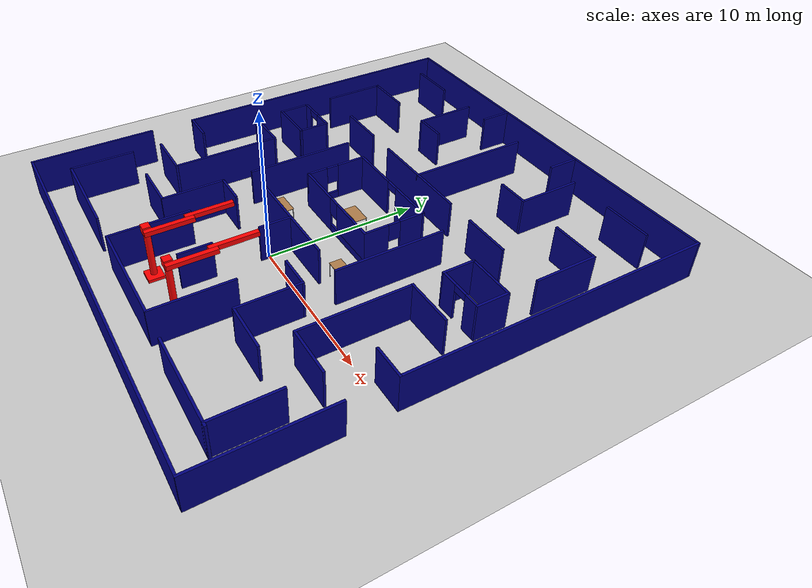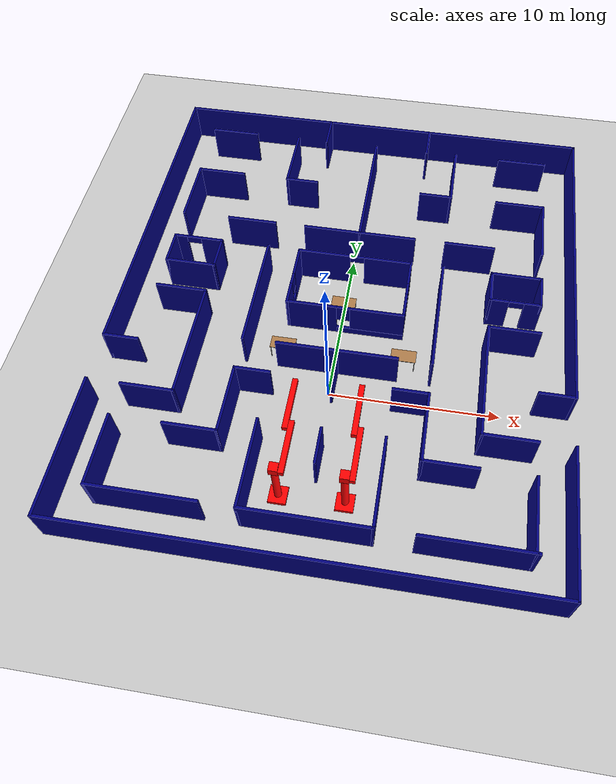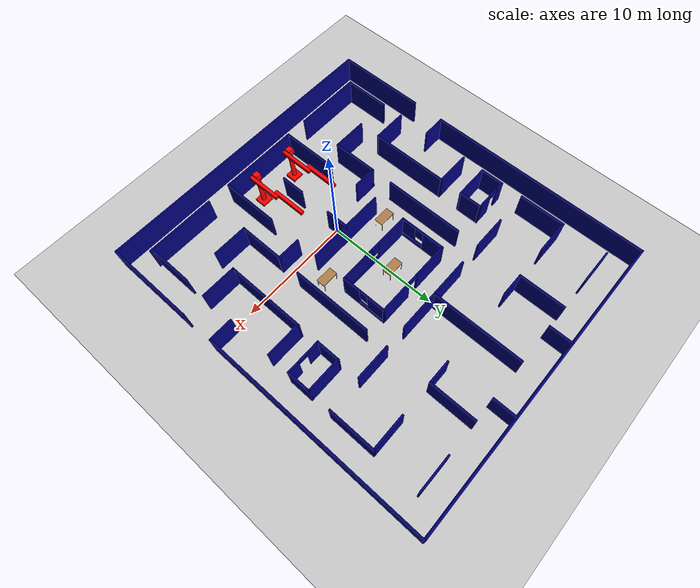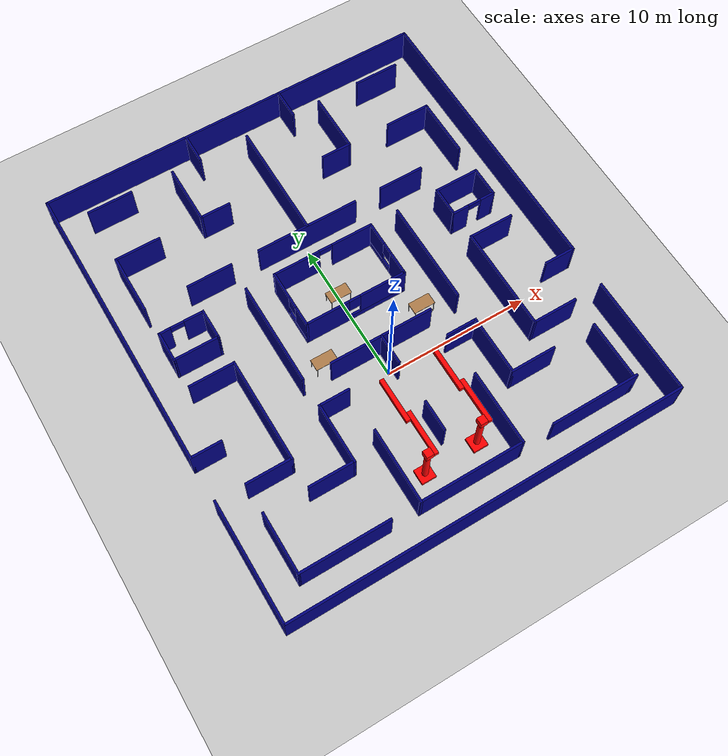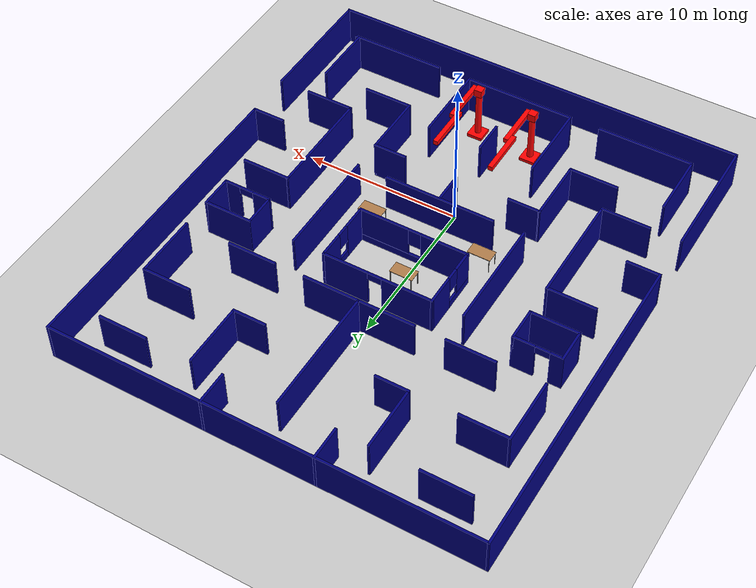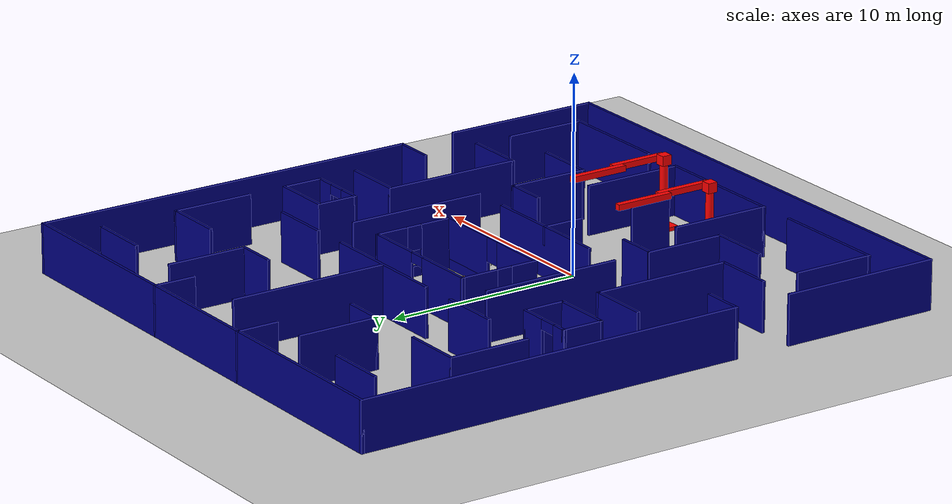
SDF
<sdf version="1.6">
 <world name="default">
  <plugin name="hello" filename="libhello.so"/>
  <light name="sun" type="directional">
   <pose>0 0 10 0 -0 0</pose>
   <diffuse>0.8 0.8 0.8 1</diffuse>
   <specular>0.2 0.2 0.2 1</specular>
   <attenuation>
    <range>1000</range>
    <constant>0.9</constant>
    <linear>0.01</linear>
    <quadratic>0.001</quadratic>
   </attenuation>
   <direction>-0.5 0.1 -0.9</direction>
  </light>
  <model name="ground_plane">
   <static>1</static>
   <link name="link">
    <collision name="collision">
     <geometry><plane><normal>0 0 1</normal><size>100 100</size></plane></geometry>
     <surface><friction><ode><mu>100</mu><mu2>50</mu2></ode></friction></surface>
    </collision>
    <visual name="visual">
     <cast_shadows>0</cast_shadows>
     <geometry><plane><normal>0 0 1</normal><size>100 100</size></plane></geometry>
     <material>
      <script><uri>file://media/materials/scripts/gazebo.material</uri><name>Gazebo/Grey</name></script>
     </material>
    </visual>
   </link>
  </model>
  <gravity>0 0 -9.8</gravity>
  <magnetic_field>6e-06 2.3e-05 -4.2e-05</magnetic_field>
  <atmosphere type="adiabatic"/>
  <physics name="default_physics" default="0" type="ode">
   <max_step_size>0.001</max_step_size>
   <real_time_factor>1</real_time_factor>
   <real_time_update_rate>1000</real_time_update_rate>
  </physics>
  <scene><ambient>0.4 0.4 0.4 1</ambient><background>0.7 0.7 0.7 1</background><shadows>1</shadows></scene>
  <spherical_coordinates>
   <surface_model>EARTH_WGS84</surface_model>
   <latitude_deg>0</latitude_deg>
   <longitude_deg>0</longitude_deg>
   <elevation>0</elevation>
   <heading_deg>0</heading_deg>
  </spherical_coordinates>
  <model name="maze">
   <pose>0.267144 4.9154 0.2059 0 -0 0</pose>
   <link name="Wall_0">
    <collision name="Wall_0_Collision">
     <geometry><box><size>27.14 0.15 2.5</size></box></geometry>
     <pose>0 0 1.25 0 -0 0</pose>
    </collision>
    <visual name="Wall_0_Visual">
     <pose>0 0 1.25 0 -0 0</pose>
     <geometry><box><size>27.14 0.15 2.5</size></box></geometry>
     <material>
      <script><uri>file://media/materials/scripts/gazebo.material</uri><name>Gazebo/Grey</name></script>
      <ambient>0 0 0.498039 1</ambient>
     </material>
     <meta><layer>0</layer></meta>
    </visual>
    <pose>0.004974 -15.5 0 0 -0 0.000741</pose>
   </link>
   <link name="Wall_10">
    <collision name="Wall_10_Collision">
     <geometry><box><size>2.15 0.15 2.5</size></box></geometry>
     <pose>0 0 1.25 0 -0 0</pose>
    </collision>
    <visual name="Wall_10_Visual">
     <pose>0 0 1.25 0 -0 0</pose>
     <geometry><box><size>2.15 0.15 2.5</size></box></geometry>
     <material>
      <script><uri>file://media/materials/scripts/gazebo.material</uri><name>Gazebo/Grey</name></script>
      <ambient>0 0 0.498039 1</ambient>
     </material>
     <meta><layer>0</layer></meta>
    </visual>
    <pose>-2.6e-05 -9.48997 0 0 -0 1.5708</pose>
   </link>
   <link name="Wall_12">
    <collision name="Wall_12_Collision">
     <geometry><box><size>5.15 0.15 2.5</size></box></geometry>
     <pose>0 0 1.25 0 -0 0</pose>
    </collision>
    <visual name="Wall_12_Visual">
     <pose>0 0 1.25 0 -0 0</pose>
     <geometry><box><size>5.15 0.15 2.5</size></box></geometry>
     <material>
      <script><uri>file://media/materials/scripts/gazebo.material</uri><name>Gazebo/Grey</name></script>
      <ambient>0 0 0.498039 1</ambient>
     </material>
     <meta><layer>0</layer></meta>
    </visual>
    <pose>3.49997 -10.99 0 0 -0 1.5708</pose>
   </link>
   <link name="Wall_14">
    <collision name="Wall_14_Collision">
     <geometry><box><size>5.15 0.15 2.5</size></box></geometry>
     <pose>0 0 1.25 0 -0 0</pose>
    </collision>
    <visual name="Wall_14_Visual">
     <pose>0 0 1.25 0 -0 0</pose>
     <geometry><box><size>5.15 0.15 2.5</size></box></geometry>
     <material>
      <script><uri>file://media/materials/scripts/gazebo.material</uri><name>Gazebo/Grey</name></script>
      <ambient>0 0 0.498039 1</ambient>
     </material>
     <meta><layer>0</layer></meta>
    </visual>
    <pose>-3.50003 -10.99 0 0 -0 1.5708</pose>
   </link>
   <link name="Wall_16">
    <collision name="Wall_16_Collision">
     <geometry><box><size>6.15 0.15 2.5</size></box></geometry>
     <pose>0 0 1.25 0 -0 0</pose>
    </collision>
    <visual name="Wall_16_Visual">
     <pose>0 0 1.25 0 -0 0</pose>
     <geometry><box><size>6.15 0.15 2.5</size></box></geometry>
     <material>
      <script><uri>file://media/materials/scripts/gazebo.material</uri><name>Gazebo/Grey</name></script>
      <ambient>0 0 0.498039 1</ambient>
     </material>
     <meta><layer>0</layer></meta>
    </visual>
    <pose>-8.50003 -13.4895 0 0 -0 0.000167</pose>
   </link>
   <link name="Wall_18">
    <collision name="Wall_18_Collision">
     <geometry><box><size>2.15 0.15 2.5</size></box></geometry>
     <pose>0 0 1.25 0 -0 0</pose>
    </collision>
    <visual name="Wall_18_Visual">
     <pose>0 0 1.25 0 -0 0</pose>
     <geometry><box><size>2.15 0.15 2.5</size></box></geometry>
     <material>
      <script><uri>file://media/materials/scripts/gazebo.material</uri><name>Gazebo/Grey</name></script>
      <ambient>0 0 0.498039 1</ambient>
     </material>
     <meta><layer>0</layer></meta>
    </visual>
    <pose>-12.5 -4.48997 0 0 -0 0</pose>
   </link>
   <link name="Wall_188">
    <collision name="Wall_188_Collision">
     <geometry><box><size>4.15 0.15 2.5</size></box></geometry>
     <pose>0 0 1.25 0 -0 0</pose>
    </collision>
    <visual name="Wall_188_Visual">
     <pose>0 0 1.25 0 -0 0</pose>
     <geometry><box><size>4.15 0.15 2.5</size></box></geometry>
     <material>
      <script><uri>file://media/materials/scripts/gazebo.material</uri><name>Gazebo/Grey</name></script>
      <ambient>0 0 0.498039 1</ambient>
     </material>
     <meta><layer>0</layer></meta>
    </visual>
    <pose>-5.50003 11.51 0 0 -0 1.5708</pose>
   </link>
   <link name="Wall_191">
    <collision name="Wall_191_Collision">
     <geometry><box><size>2.15 0.15 2.5</size></box></geometry>
     <pose>0 0 1.25 0 -0 0</pose>
    </collision>
    <visual name="Wall_191_Visual">
     <pose>0 0 1.25 0 -0 0</pose>
     <geometry><box><size>2.15 0.15 2.5</size></box></geometry>
     <material>
      <script><uri>file://media/materials/scripts/gazebo.material</uri><name>Gazebo/Grey</name></script>
      <ambient>0 0 0.498039 1</ambient>
     </material>
     <meta><layer>0</layer></meta>
    </visual>
    <pose>-4.50003 9.51003 0 0 -0 0</pose>
   </link>
   <link name="Wall_193">
    <collision name="Wall_193_Collision">
     <geometry><box><size>2.15 0.15 2.5</size></box></geometry>
     <pose>0 0 1.25 0 -0 0</pose>
    </collision>
    <visual name="Wall_193_Visual">
     <pose>0 0 1.25 0 -0 0</pose>
     <geometry><box><size>2.15 0.15 2.5</size></box></geometry>
     <material>
      <script><uri>file://media/materials/scripts/gazebo.material</uri><name>Gazebo/Grey</name></script>
      <ambient>0 0 0.498039 1</ambient>
     </material>
     <meta><layer>0</layer></meta>
    </visual>
    <pose>-3.50003 14.51 0 0 -0 1.5708</pose>
   </link>
   <link name="Wall_195">
    <collision name="Wall_195_Collision">
     <geometry><box><size>2.15 0.15 2.5</size></box></geometry>
     <pose>0 0 1.25 0 -0 0</pose>
    </collision>
    <visual name="Wall_195_Visual">
     <pose>0 0 1.25 0 -0 0</pose>
     <geometry><box><size>2.15 0.15 2.5</size></box></geometry>
     <material>
      <script><uri>file://media/materials/scripts/gazebo.material</uri><name>Gazebo/Grey</name></script>
      <ambient>0 0 0.498039 1</ambient>
     </material>
     <meta><layer>0</layer></meta>
    </visual>
    <pose>3.49997 14.51 0 0 0 -1.5708</pose>
   </link>
   <link name="Wall_197">
    <pose>-2.6e-05 -0.489973 0 0 -0 0</pose>
    <visual name="Wall_197_Visual_0">
     <pose>-2.03649 0 1.25 0 -0 0</pose>
     <geometry><box><size>3.07701 0.15 2.5</size></box></geometry>
     <material>
      <script><uri>file://media/materials/scripts/gazebo.material</uri><name>Gazebo/Grey</name></script>
      <ambient>0 0 0.498039 1</ambient>
     </material>
     <meta><layer>0</layer></meta>
    </visual>
    <collision name="Wall_197_Collision_0">
     <geometry><box><size>3.07701 0.15 2.5</size></box></geometry>
     <pose>-2.03649 0 1.25 0 -0 0</pose>
    </collision>
    <visual name="Wall_197_Visual_1">
     <pose>1.53851 0 0.25 0 -0 0</pose>
     <geometry><box><size>4.07299 0.15 0.5</size></box></geometry>
     <material>
      <script><uri>file://media/materials/scripts/gazebo.material</uri><name>Gazebo/Grey</name></script>
      <ambient>0 0 0.498039 1</ambient>
     </material>
     <meta><layer>0</layer></meta>
    </visual>
    <collision name="Wall_197_Collision_1">
     <geometry><box><size>4.07299 0.15 0.5</size></box></geometry>
     <pose>1.53851 0 0.25 0 -0 0</pose>
    </collision>
    <visual name="Wall_197_Visual_2">
     <pose>1.9385 0 1.5 0 -0 0</pose>
     <geometry><box><size>3.27299 0.15 2</size></box></geometry>
     <material>
      <script><uri>file://media/materials/scripts/gazebo.material</uri><name>Gazebo/Grey</name></script>
      <ambient>0 0 0.498039 1</ambient>
     </material>
     <meta><layer>0</layer></meta>
    </visual>
    <collision name="Wall_197_Collision_2">
     <geometry><box><size>3.27299 0.15 2</size></box></geometry>
     <pose>1.9385 0 1.5 0 -0 0</pose>
    </collision>
    <visual name="Wall_197_Visual_3">
     <pose>-0.097991 0 1.9 0 -0 0</pose>
     <geometry><box><size>0.8 0.15 1.2</size></box></geometry>
     <material>
      <script><uri>file://media/materials/scripts/gazebo.material</uri><name>Gazebo/Grey</name></script>
      <ambient>0 0 0.498039 1</ambient>
     </material>
     <meta><layer>0</layer></meta>
    </visual>
    <collision name="Wall_197_Collision_3">
     <geometry><box><size>0.8 0.15 1.2</size></box></geometry>
     <pose>-0.097991 0 1.9 0 -0 0</pose>
    </collision>
   </link>
   <link name="Wall_199">
    <pose>3.49997 1.51003 0 0 -0 1.5708</pose>
    <visual name="Wall_199_Visual_0">
     <pose>-1.2422 0 1.25 0 -0 0</pose>
     <geometry><box><size>1.6656 0.15 2.5</size></box></geometry>
     <material>
      <script><uri>file://media/materials/scripts/gazebo.material</uri><name>Gazebo/Grey</name></script>
      <ambient>0 0 0.498039 1</ambient>
     </material>
     <meta><layer>0</layer></meta>
    </visual>
    <collision name="Wall_199_Collision_0">
     <geometry><box><size>1.6656 0.15 2.5</size></box></geometry>
     <pose>-1.2422 0 1.25 0 -0 0</pose>
    </collision>
    <visual name="Wall_199_Visual_1">
     <pose>0.832802 0 0.25 0 -0 0</pose>
     <geometry><box><size>2.4844 0.15 0.5</size></box></geometry>
     <material>
      <script><uri>file://media/materials/scripts/gazebo.material</uri><name>Gazebo/Grey</name></script>
      <ambient>0 0 0.498039 1</ambient>
     </material>
     <meta><layer>0</layer></meta>
    </visual>
    <collision name="Wall_199_Collision_1">
     <geometry><box><size>2.4844 0.15 0.5</size></box></geometry>
     <pose>0.832802 0 0.25 0 -0 0</pose>
    </collision>
    <visual name="Wall_199_Visual_2">
     <pose>1.2328 0 1.5 0 -0 0</pose>
     <geometry><box><size>1.6844 0.15 2</size></box></geometry>
     <material>
      <script><uri>file://media/materials/scripts/gazebo.material</uri><name>Gazebo/Grey</name></script>
      <ambient>0 0 0.498039 1</ambient>
     </material>
     <meta><layer>0</layer></meta>
    </visual>
    <collision name="Wall_199_Collision_2">
     <geometry><box><size>1.6844 0.15 2</size></box></geometry>
     <pose>1.2328 0 1.5 0 -0 0</pose>
    </collision>
    <visual name="Wall_199_Visual_3">
     <pose>-0.009396 0 1.9 0 -0 0</pose>
     <geometry><box><size>0.8 0.15 1.2</size></box></geometry>
     <material>
      <script><uri>file://media/materials/scripts/gazebo.material</uri><name>Gazebo/Grey</name></script>
      <ambient>0 0 0.498039 1</ambient>
     </material>
     <meta><layer>0</layer></meta>
    </visual>
    <collision name="Wall_199_Collision_3">
     <geometry><box><size>0.8 0.15 1.2</size></box></geometry>
     <pose>-0.009396 0 1.9 0 -0 0</pose>
    </collision>
   </link>
   <link name="Wall_2">
    <collision name="Wall_2_Collision">
     <geometry><box><size>8.15 0.15 2.5</size></box></geometry>
     <pose>0 0 1.25 0 -0 0</pose>
    </collision>
    <visual name="Wall_2_Visual">
     <pose>0 0 1.25 0 -0 0</pose>
     <geometry><box><size>8.15 0.15 2.5</size></box></geometry>
     <material>
      <script><uri>file://media/materials/scripts/gazebo.material</uri><name>Gazebo/Grey</name></script>
      <ambient>0 0 0.498039 1</ambient>
     </material>
     <meta><layer>0</layer></meta>
    </visual>
    <pose>-13.5 -11.49 0 0 -0 1.5708</pose>
   </link>
   <link name="Wall_20">
    <collision name="Wall_20_Collision">
     <geometry><box><size>20.15 0.15 2.5</size></box></geometry>
     <pose>0 0 1.25 0 -0 0</pose>
    </collision>
    <visual name="Wall_20_Visual">
     <pose>0 0 1.25 0 -0 0</pose>
     <geometry><box><size>20.15 0.15 2.5</size></box></geometry>
     <material>
      <script><uri>file://media/materials/scripts/gazebo.material</uri><name>Gazebo/Grey</name></script>
      <ambient>0 0 0.498039 1</ambient>
     </material>
     <meta><layer>0</layer></meta>
    </visual>
    <pose>13.5 5.51003 0 0 -0 1.5708</pose>
   </link>
   <link name="Wall_201">
    <pose>-3.50003 1.51003 0 0 0 -1.5708</pose>
    <visual name="Wall_201_Visual_0">
     <pose>-1.09685 0 1.25 0 -0 0</pose>
     <geometry><box><size>1.9563 0.15 2.5</size></box></geometry>
     <material>
      <script><uri>file://media/materials/scripts/gazebo.material</uri><name>Gazebo/Grey</name></script>
      <ambient>0 0 0.498039 1</ambient>
     </material>
     <meta><layer>0</layer></meta>
    </visual>
    <collision name="Wall_201_Collision_0">
     <geometry><box><size>1.9563 0.15 2.5</size></box></geometry>
     <pose>-1.09685 0 1.25 0 -0 0</pose>
    </collision>
    <visual name="Wall_201_Visual_1">
     <pose>0.97815 0 0.25 0 -0 0</pose>
     <geometry><box><size>2.1937 0.15 0.5</size></box></geometry>
     <material>
      <script><uri>file://media/materials/scripts/gazebo.material</uri><name>Gazebo/Grey</name></script>
      <ambient>0 0 0.498039 1</ambient>
     </material>
     <meta><layer>0</layer></meta>
    </visual>
    <collision name="Wall_201_Collision_1">
     <geometry><box><size>2.1937 0.15 0.5</size></box></geometry>
     <pose>0.97815 0 0.25 0 -0 0</pose>
    </collision>
    <visual name="Wall_201_Visual_2">
     <pose>1.37815 0 1.5 0 -0 0</pose>
     <geometry><box><size>1.3937 0.15 2</size></box></geometry>
     <material>
      <script><uri>file://media/materials/scripts/gazebo.material</uri><name>Gazebo/Grey</name></script>
      <ambient>0 0 0.498039 1</ambient>
     </material>
     <meta><layer>0</layer></meta>
    </visual>
    <collision name="Wall_201_Collision_2">
     <geometry><box><size>1.3937 0.15 2</size></box></geometry>
     <pose>1.37815 0 1.5 0 -0 0</pose>
    </collision>
    <visual name="Wall_201_Visual_3">
     <pose>0.2813 0 1.9 0 -0 0</pose>
     <geometry><box><size>0.8 0.15 1.2</size></box></geometry>
     <material>
      <script><uri>file://media/materials/scripts/gazebo.material</uri><name>Gazebo/Grey</name></script>
      <ambient>0 0 0.498039 1</ambient>
     </material>
     <meta><layer>0</layer></meta>
    </visual>
    <collision name="Wall_201_Collision_3">
     <geometry><box><size>0.8 0.15 1.2</size></box></geometry>
     <pose>0.2813 0 1.9 0 -0 0</pose>
    </collision>
   </link>
   <link name="Wall_202">
    <collision name="Wall_202_Collision">
     <geometry><box><size>0.15 0.15 2.5</size></box></geometry>
     <pose>0 0 1.25 0 -0 0</pose>
    </collision>
    <visual name="Wall_202_Visual">
     <pose>0 0 1.25 0 -0 0</pose>
     <geometry><box><size>0.15 0.15 2.5</size></box></geometry>
     <material>
      <script><uri>file://media/materials/scripts/gazebo.material</uri><name>Gazebo/Grey</name></script>
      <ambient>0 0 0.498039 1</ambient>
     </material>
     <meta><layer>0</layer></meta>
    </visual>
    <pose>-3.50003 -0.489973 0 0 -0 0</pose>
   </link>
   <link name="Wall_204">
    <collision name="Wall_204_Collision">
     <geometry><box><size>4.15 0.15 2.5</size></box></geometry>
     <pose>0 0 1.25 0 -0 0</pose>
    </collision>
    <visual name="Wall_204_Visual">
     <pose>0 0 1.25 0 -0 0</pose>
     <geometry><box><size>4.15 0.15 2.5</size></box></geometry>
     <material>
      <script><uri>file://media/materials/scripts/gazebo.material</uri><name>Gazebo/Grey</name></script>
      <ambient>0 0 0.498039 1</ambient>
     </material>
     <meta><layer>0</layer></meta>
    </visual>
    <pose>5.49997 11.51 0 0 -0 1.5708</pose>
   </link>
   <link name="Wall_206">
    <collision name="Wall_206_Collision">
     <geometry><box><size>2.15 0.15 2.5</size></box></geometry>
     <pose>0 0 1.25 0 -0 0</pose>
    </collision>
    <visual name="Wall_206_Visual">
     <pose>0 0 1.25 0 -0 0</pose>
     <geometry><box><size>2.15 0.15 2.5</size></box></geometry>
     <material>
      <script><uri>file://media/materials/scripts/gazebo.material</uri><name>Gazebo/Grey</name></script>
      <ambient>0 0 0.498039 1</ambient>
     </material>
     <meta><layer>0</layer></meta>
    </visual>
    <pose>4.49997 9.51003 0 0 -0 0</pose>
   </link>
   <link name="Wall_208">
    <collision name="Wall_208_Collision">
     <geometry><box><size>8.15 0.15 2.5</size></box></geometry>
     <pose>0 0 1.25 0 -0 0</pose>
    </collision>
    <visual name="Wall_208_Visual">
     <pose>0 0 1.25 0 -0 0</pose>
     <geometry><box><size>8.15 0.15 2.5</size></box></geometry>
     <material>
      <script><uri>file://media/materials/scripts/gazebo.material</uri><name>Gazebo/Grey</name></script>
      <ambient>0 0 0.498039 1</ambient>
     </material>
     <meta><layer>0</layer></meta>
    </visual>
    <pose>-2.6e-05 9.51003 0 0 -0 1.5708</pose>
   </link>
   <link name="Wall_210">
    <collision name="Wall_210_Collision">
     <geometry><box><size>7.15 0.15 2.5</size></box></geometry>
     <pose>0 0 1.25 0 -0 0</pose>
    </collision>
    <visual name="Wall_210_Visual">
     <pose>0 0 1.25 0 -0 0</pose>
     <geometry><box><size>7.15 0.15 2.5</size></box></geometry>
     <material>
      <script><uri>file://media/materials/scripts/gazebo.material</uri><name>Gazebo/Grey</name></script>
      <ambient>0 0 0.498039 1</ambient>
     </material>
     <meta><layer>0</layer></meta>
    </visual>
    <pose>-2.6e-05 5.51003 0 0 -0 0</pose>
   </link>
   <link name="Wall_212">
    <pose>-2.6e-05 3.51003 0 0 -0 0</pose>
    <visual name="Wall_212_Visual_0">
     <pose>-1.93418 0 1.25 0 -0 0</pose>
     <geometry><box><size>3.28164 0.15 2.5</size></box></geometry>
     <material>
      <script><uri>file://media/materials/scripts/gazebo.material</uri><name>Gazebo/Grey</name></script>
      <ambient>0 0 0.498039 1</ambient>
     </material>
     <meta><layer>0</layer></meta>
    </visual>
    <collision name="Wall_212_Collision_0">
     <geometry><box><size>3.28164 0.15 2.5</size></box></geometry>
     <pose>-1.93418 0 1.25 0 -0 0</pose>
    </collision>
    <visual name="Wall_212_Visual_1">
     <pose>2.09082 0 1.25 0 -0 0</pose>
     <geometry><box><size>2.96836 0.15 2.5</size></box></geometry>
     <material>
      <script><uri>file://media/materials/scripts/gazebo.material</uri><name>Gazebo/Grey</name></script>
      <ambient>0 0 0.498039 1</ambient>
     </material>
     <meta><layer>0</layer></meta>
    </visual>
    <collision name="Wall_212_Collision_1">
     <geometry><box><size>2.96836 0.15 2.5</size></box></geometry>
     <pose>2.09082 0 1.25 0 -0 0</pose>
    </collision>
    <visual name="Wall_212_Visual_2">
     <pose>0.156638 0 2.25 0 -0 0</pose>
     <geometry><box><size>0.9 0.15 0.5</size></box></geometry>
     <material>
      <script><uri>file://media/materials/scripts/gazebo.material</uri><name>Gazebo/Grey</name></script>
      <ambient>0 0 0.498039 1</ambient>
     </material>
     <meta><layer>0</layer></meta>
    </visual>
    <collision name="Wall_212_Collision_2">
     <geometry><box><size>0.9 0.15 0.5</size></box></geometry>
     <pose>0.156638 0 2.25 0 -0 0</pose>
    </collision>
   </link>
   <link name="Wall_215">
    <collision name="Wall_215_Collision">
     <geometry><box><size>3.15 0.15 2.5</size></box></geometry>
     <pose>0 0 1.25 0 -0 0</pose>
    </collision>
    <visual name="Wall_215_Visual">
     <pose>0 0 1.25 0 -0 0</pose>
     <geometry><box><size>3.15 0.15 2.5</size></box></geometry>
     <material>
      <script><uri>file://media/materials/scripts/gazebo.material</uri><name>Gazebo/Grey</name></script>
      <ambient>0 0 0.498039 1</ambient>
     </material>
     <meta><layer>0</layer></meta>
    </visual>
    <pose>6.99997 5.51003 0 0 -0 0</pose>
   </link>
   <link name="Wall_217">
    <collision name="Wall_217_Collision">
     <geometry><box><size>7.15 0.15 2.5</size></box></geometry>
     <pose>0 0 1.25 0 -0 0</pose>
    </collision>
    <visual name="Wall_217_Visual">
     <pose>0 0 1.25 0 -0 0</pose>
     <geometry><box><size>7.15 0.15 2.5</size></box></geometry>
     <material>
      <script><uri>file://media/materials/scripts/gazebo.material</uri><name>Gazebo/Grey</name></script>
      <ambient>0 0 0.498039 1</ambient>
     </material>
     <meta><layer>0</layer></meta>
    </visual>
    <pose>5.49997 0.010027 0 0 -0 1.5708</pose>
   </link>
   <link name="Wall_219">
    <collision name="Wall_219_Collision">
     <geometry><box><size>3.15 0.15 2.5</size></box></geometry>
     <pose>0 0 1.25 0 -0 0</pose>
    </collision>
    <visual name="Wall_219_Visual">
     <pose>0 0 1.25 0 -0 0</pose>
     <geometry><box><size>3.15 0.15 2.5</size></box></geometry>
     <material>
      <script><uri>file://media/materials/scripts/gazebo.material</uri><name>Gazebo/Grey</name></script>
      <ambient>0 0 0.498039 1</ambient>
     </material>
     <meta><layer>0</layer></meta>
    </visual>
    <pose>9.99997 -0.489973 0 0 -0 0</pose>
   </link>
   <link name="Wall_22">
    <collision name="Wall_22_Collision">
     <geometry><box><size>4.15 0.15 2.5</size></box></geometry>
     <pose>0 0 1.25 0 -0 0</pose>
    </collision>
    <visual name="Wall_22_Visual">
     <pose>0 0 1.25 0 -0 0</pose>
     <geometry><box><size>4.15 0.15 2.5</size></box></geometry>
     <material>
      <script><uri>file://media/materials/scripts/gazebo.material</uri><name>Gazebo/Grey</name></script>
      <ambient>0 0 0.498039 1</ambient>
     </material>
     <meta><layer>0</layer></meta>
    </visual>
    <pose>-11.5 -11.49 0 0 -0 1.5708</pose>
   </link>
   <link name="Wall_221">
    <collision name="Wall_221_Collision">
     <geometry><box><size>7.15 0.15 2.5</size></box></geometry>
     <pose>0 0 1.25 0 -0 0</pose>
    </collision>
    <visual name="Wall_221_Visual">
     <pose>0 0 1.25 0 -0 0</pose>
     <geometry><box><size>7.15 0.15 2.5</size></box></geometry>
     <material>
      <script><uri>file://media/materials/scripts/gazebo.material</uri><name>Gazebo/Grey</name></script>
      <ambient>0 0 0.498039 1</ambient>
     </material>
     <meta><layer>0</layer></meta>
    </visual>
    <pose>8.49997 -3.98997 0 0 -0 1.5708</pose>
   </link>
   <link name="Wall_223">
    <collision name="Wall_223_Collision">
     <geometry><box><size>3.15 0.15 2.5</size></box></geometry>
     <pose>0 0 1.25 0 -0 0</pose>
    </collision>
    <visual name="Wall_223_Visual">
     <pose>0 0 1.25 0 -0 0</pose>
     <geometry><box><size>3.15 0.15 2.5</size></box></geometry>
     <material>
      <script><uri>file://media/materials/scripts/gazebo.material</uri><name>Gazebo/Grey</name></script>
      <ambient>0 0 0.498039 1</ambient>
     </material>
     <meta><layer>0</layer></meta>
    </visual>
    <pose>9.99997 -7.48997 0 0 -0 0</pose>
   </link>
   <link name="Wall_225">
    <collision name="Wall_225_Collision">
     <geometry><box><size>2.15 0.15 2.5</size></box></geometry>
     <pose>0 0 1.25 0 -0 0</pose>
    </collision>
    <visual name="Wall_225_Visual">
     <pose>0 0 1.25 0 -0 0</pose>
     <geometry><box><size>2.15 0.15 2.5</size></box></geometry>
     <material>
      <script><uri>file://media/materials/scripts/gazebo.material</uri><name>Gazebo/Grey</name></script>
      <ambient>0 0 0.498039 1</ambient>
     </material>
     <meta><layer>0</layer></meta>
    </visual>
    <pose>12.5 -4.48997 0 0 -0 0</pose>
   </link>
   <link name="Wall_227">
    <collision name="Wall_227_Collision">
     <geometry><box><size>2.15 0.15 2.5</size></box></geometry>
     <pose>0 0 1.25 0 -0 0</pose>
    </collision>
    <visual name="Wall_227_Visual">
     <pose>0 0 1.25 0 -0 0</pose>
     <geometry><box><size>2.15 0.15 2.5</size></box></geometry>
     <material>
      <script><uri>file://media/materials/scripts/gazebo.material</uri><name>Gazebo/Grey</name></script>
      <ambient>0 0 0.498039 1</ambient>
     </material>
     <meta><layer>0</layer></meta>
    </visual>
    <pose>8.49997 2.51003 0 0 -0 1.5708</pose>
   </link>
   <link name="Wall_229">
    <collision name="Wall_229_Collision">
     <geometry><box><size>2.15 0.15 2.5</size></box></geometry>
     <pose>0 0 1.25 0 -0 0</pose>
    </collision>
    <visual name="Wall_229_Visual">
     <pose>0 0 1.25 0 -0 0</pose>
     <geometry><box><size>2.15 0.15 2.5</size></box></geometry>
     <material>
      <script><uri>file://media/materials/scripts/gazebo.material</uri><name>Gazebo/Grey</name></script>
      <ambient>0 0 0.498039 1</ambient>
     </material>
     <meta><layer>0</layer></meta>
    </visual>
    <pose>11.5 2.51003 0 0 -0 1.5708</pose>
   </link>
   <link name="Wall_231">
    <pose>9.99997 1.51003 0 0 -0 0</pose>
    <visual name="Wall_231_Visual_0">
     <pose>-0.98595 0 1.25 0 -0 0</pose>
     <geometry><box><size>1.1781 0.15 2.5</size></box></geometry>
     <material>
      <script><uri>file://media/materials/scripts/gazebo.material</uri><name>Gazebo/Grey</name></script>
      <ambient>0 0 0.498039 1</ambient>
     </material>
     <meta><layer>0</layer></meta>
    </visual>
    <collision name="Wall_231_Collision_0">
     <geometry><box><size>1.1781 0.15 2.5</size></box></geometry>
     <pose>-0.98595 0 1.25 0 -0 0</pose>
    </collision>
    <visual name="Wall_231_Visual_1">
     <pose>1.03905 0 1.25 0 -0 0</pose>
     <geometry><box><size>1.0719 0.15 2.5</size></box></geometry>
     <material>
      <script><uri>file://media/materials/scripts/gazebo.material</uri><name>Gazebo/Grey</name></script>
      <ambient>0 0 0.498039 1</ambient>
     </material>
     <meta><layer>0</layer></meta>
    </visual>
    <collision name="Wall_231_Collision_1">
     <geometry><box><size>1.0719 0.15 2.5</size></box></geometry>
     <pose>1.03905 0 1.25 0 -0 0</pose>
    </collision>
    <visual name="Wall_231_Visual_2">
     <pose>0.053101 0 2.25 0 -0 0</pose>
     <geometry><box><size>0.9 0.15 0.5</size></box></geometry>
     <material>
      <script><uri>file://media/materials/scripts/gazebo.material</uri><name>Gazebo/Grey</name></script>
      <ambient>0 0 0.498039 1</ambient>
     </material>
     <meta><layer>0</layer></meta>
    </visual>
    <collision name="Wall_231_Collision_2">
     <geometry><box><size>0.9 0.15 0.5</size></box></geometry>
     <pose>0.053101 0 2.25 0 -0 0</pose>
    </collision>
   </link>
   <link name="Wall_233">
    <collision name="Wall_233_Collision">
     <geometry><box><size>3.15 0.15 2.5</size></box></geometry>
     <pose>0 0 1.25 0 -0 0</pose>
    </collision>
    <visual name="Wall_233_Visual">
     <pose>0 0 1.25 0 -0 0</pose>
     <geometry><box><size>3.15 0.15 2.5</size></box></geometry>
     <material>
      <script><uri>file://media/materials/scripts/gazebo.material</uri><name>Gazebo/Grey</name></script>
      <ambient>0 0 0.498039 1</ambient>
     </material>
     <meta><layer>0</layer></meta>
    </visual>
    <pose>9.99997 3.51003 0 0 -0 0</pose>
   </link>
   <link name="Wall_235">
    <collision name="Wall_235_Collision">
     <geometry><box><size>3.15 0.15 2.5</size></box></geometry>
     <pose>0 0 1.25 0 -0 0</pose>
    </collision>
    <visual name="Wall_235_Visual">
     <pose>0 0 1.25 0 -0 0</pose>
     <geometry><box><size>3.15 0.15 2.5</size></box></geometry>
     <material>
      <script><uri>file://media/materials/scripts/gazebo.material</uri><name>Gazebo/Grey</name></script>
      <ambient>0 0 0.498039 1</ambient>
     </material>
     <meta><layer>0</layer></meta>
    </visual>
    <pose>9.99997 9.51003 0 0 -0 0</pose>
   </link>
   <link name="Wall_236">
    <collision name="Wall_236_Collision">
     <geometry><box><size>4.15 0.15 2.5</size></box></geometry>
     <pose>0 0 1.25 0 -0 0</pose>
    </collision>
    <visual name="Wall_236_Visual">
     <pose>0 0 1.25 0 -0 0</pose>
     <geometry><box><size>4.15 0.15 2.5</size></box></geometry>
     <material>
      <script><uri>file://media/materials/scripts/gazebo.material</uri><name>Gazebo/Grey</name></script>
      <ambient>0 0 0.498039 1</ambient>
     </material>
     <meta><layer>0</layer></meta>
    </visual>
    <pose>11.5 7.51003 0 0 0 -1.5708</pose>
   </link>
   <link name="Wall_238">
    <collision name="Wall_238_Collision">
     <geometry><box><size>3.15 0.15 2.5</size></box></geometry>
     <pose>0 0 1.25 0 -0 0</pose>
    </collision>
    <visual name="Wall_238_Visual">
     <pose>0 0 1.25 0 -0 0</pose>
     <geometry><box><size>3.15 0.15 2.5</size></box></geometry>
     <material>
      <script><uri>file://media/materials/scripts/gazebo.material</uri><name>Gazebo/Grey</name></script>
      <ambient>0 0 0.498039 1</ambient>
     </material>
     <meta><layer>0</layer></meta>
    </visual>
    <pose>9.99997 13.51 0 0 -0 0</pose>
   </link>
   <link name="Wall_24">
    <collision name="Wall_24_Collision">
     <geometry><box><size>7.15 0.15 2.5</size></box></geometry>
     <pose>0 0 1.25 0 -0 0</pose>
    </collision>
    <visual name="Wall_24_Visual">
     <pose>0 0 1.25 0 -0 0</pose>
     <geometry><box><size>7.15 0.15 2.5</size></box></geometry>
     <material>
      <script><uri>file://media/materials/scripts/gazebo.material</uri><name>Gazebo/Grey</name></script>
      <ambient>0 0 0.498039 1</ambient>
     </material>
     <meta><layer>0</layer></meta>
    </visual>
    <pose>-2.6e-05 -13.49 0 0 -0 0</pose>
   </link>
   <link name="Wall_240">
    <collision name="Wall_240_Collision">
     <geometry><box><size>7.15 0.15 2.5</size></box></geometry>
     <pose>0 0 1.25 0 -0 0</pose>
    </collision>
    <visual name="Wall_240_Visual">
     <pose>0 0 1.25 0 -0 0</pose>
     <geometry><box><size>7.15 0.15 2.5</size></box></geometry>
     <material>
      <script><uri>file://media/materials/scripts/gazebo.material</uri><name>Gazebo/Grey</name></script>
      <ambient>0 0 0.498039 1</ambient>
     </material>
     <meta><layer>0</layer></meta>
    </visual>
    <pose>-2.6e-05 -3.48997 0 0 -0 0</pose>
   </link>
   <link name="Wall_242">
    <collision name="Wall_242_Collision">
     <geometry><box><size>2.15 0.15 2.5</size></box></geometry>
     <pose>0 0 1.25 0 -0 0</pose>
    </collision>
    <visual name="Wall_242_Visual">
     <pose>0 0 1.25 0 -0 0</pose>
     <geometry><box><size>2.15 0.15 2.5</size></box></geometry>
     <material>
      <script><uri>file://media/materials/scripts/gazebo.material</uri><name>Gazebo/Grey</name></script>
      <ambient>0 0 0.498039 1</ambient>
     </material>
     <meta><layer>0</layer></meta>
    </visual>
    <pose>-2.6e-05 -4.48997 0 0 0 -1.5708</pose>
   </link>
   <link name="Wall_26">
    <collision name="Wall_26_Collision">
     <geometry><box><size>6.15 0.15 2.5</size></box></geometry>
     <pose>0 0 1.25 0 -0 0</pose>
    </collision>
    <visual name="Wall_26_Visual">
     <pose>0 0 1.25 0 -0 0</pose>
     <geometry><box><size>6.15 0.15 2.5</size></box></geometry>
     <material>
      <script><uri>file://media/materials/scripts/gazebo.material</uri><name>Gazebo/Grey</name></script>
      <ambient>0 0 0.498039 1</ambient>
     </material>
     <meta><layer>0</layer></meta>
    </visual>
    <pose>8.68456 -13.49 0 0 -0 0</pose>
   </link>
   <link name="Wall_28">
    <collision name="Wall_28_Collision">
     <geometry><box><size>3.15 0.15 2.5</size></box></geometry>
     <pose>0 0 1.25 0 -0 0</pose>
    </collision>
    <visual name="Wall_28_Visual">
     <pose>0 0 1.25 0 -0 0</pose>
     <geometry><box><size>3.15 0.15 2.5</size></box></geometry>
     <material>
      <script><uri>file://media/materials/scripts/gazebo.material</uri><name>Gazebo/Grey</name></script>
      <ambient>0 0 0.498039 1</ambient>
     </material>
     <meta><layer>0</layer></meta>
    </visual>
    <pose>-10 -7.48997 0 0 -0 0</pose>
   </link>
   <link name="Wall_30">
    <collision name="Wall_30_Collision">
     <geometry><box><size>2.15 0.15 2.5</size></box></geometry>
     <pose>0 0 1.25 0 -0 0</pose>
    </collision>
    <visual name="Wall_30_Visual">
     <pose>0 0 1.25 0 -0 0</pose>
     <geometry><box><size>2.15 0.15 2.5</size></box></geometry>
     <material>
      <script><uri>file://media/materials/scripts/gazebo.material</uri><name>Gazebo/Grey</name></script>
      <ambient>0 0 0.498039 1</ambient>
     </material>
     <meta><layer>0</layer></meta>
    </visual>
    <pose>4.49997 -5.48997 0 0 -0 0</pose>
   </link>
   <link name="Wall_32">
    <collision name="Wall_32_Collision">
     <geometry><box><size>3.15 0.15 2.5</size></box></geometry>
     <pose>0 0 1.25 0 -0 0</pose>
    </collision>
    <visual name="Wall_32_Visual">
     <pose>0 0 1.25 0 -0 0</pose>
     <geometry><box><size>3.15 0.15 2.5</size></box></geometry>
     <material>
      <script><uri>file://media/materials/scripts/gazebo.material</uri><name>Gazebo/Grey</name></script>
      <ambient>0 0 0.498039 1</ambient>
     </material>
     <meta><layer>0</layer></meta>
    </visual>
    <pose>6.99997 -9.48997 0 0 -0 0</pose>
   </link>
   <link name="Wall_34">
    <collision name="Wall_34_Collision">
     <geometry><box><size>4.15 0.15 2.5</size></box></geometry>
     <pose>0 0 1.25 0 -0 0</pose>
    </collision>
    <visual name="Wall_34_Visual">
     <pose>0 0 1.25 0 -0 0</pose>
     <geometry><box><size>4.15 0.15 2.5</size></box></geometry>
     <material>
      <script><uri>file://media/materials/scripts/gazebo.material</uri><name>Gazebo/Grey</name></script>
      <ambient>0 0 0.498039 1</ambient>
     </material>
     <meta><layer>0</layer></meta>
    </visual>
    <pose>5.49997 -7.48997 0 0 -0 1.5708</pose>
   </link>
   <link name="Wall_36">
    <collision name="Wall_36_Collision">
     <geometry><box><size>2.15 0.15 2.5</size></box></geometry>
     <pose>0 0 1.25 0 -0 0</pose>
    </collision>
    <visual name="Wall_36_Visual">
     <pose>0 0 1.25 0 -0 0</pose>
     <geometry><box><size>2.15 0.15 2.5</size></box></geometry>
     <material>
      <script><uri>file://media/materials/scripts/gazebo.material</uri><name>Gazebo/Grey</name></script>
      <ambient>0 0 0.498039 1</ambient>
     </material>
     <meta><layer>0</layer></meta>
    </visual>
    <pose>-4.50003 -5.48997 0 0 -0 0</pose>
   </link>
   <link name="Wall_38">
    <collision name="Wall_38_Collision">
     <geometry><box><size>3.15 0.15 2.5</size></box></geometry>
     <pose>0 0 1.25 0 -0 0</pose>
    </collision>
    <visual name="Wall_38_Visual">
     <pose>0 0 1.25 0 -0 0</pose>
     <geometry><box><size>3.15 0.15 2.5</size></box></geometry>
     <material>
      <script><uri>file://media/materials/scripts/gazebo.material</uri><name>Gazebo/Grey</name></script>
      <ambient>0 0 0.498039 1</ambient>
     </material>
     <meta><layer>0</layer></meta>
    </visual>
    <pose>-7.00003 -9.48997 0 0 -0 0</pose>
   </link>
   <link name="Wall_4">
    <collision name="Wall_4_Collision">
     <geometry><box><size>8.15 0.15 2.5</size></box></geometry>
     <pose>0 0 1.25 0 -0 0</pose>
    </collision>
    <visual name="Wall_4_Visual">
     <pose>0 0 1.25 0 -0 0</pose>
     <geometry><box><size>8.15 0.15 2.5</size></box></geometry>
     <material>
      <script><uri>file://media/materials/scripts/gazebo.material</uri><name>Gazebo/Grey</name></script>
      <ambient>0 0 0.498039 1</ambient>
     </material>
     <meta><layer>0</layer></meta>
    </visual>
    <pose>13.5 -11.49 0 0 -0 1.5708</pose>
   </link>
   <link name="Wall_40">
    <collision name="Wall_40_Collision">
     <geometry><box><size>4.15 0.15 2.5</size></box></geometry>
     <pose>0 0 1.25 0 -0 0</pose>
    </collision>
    <visual name="Wall_40_Visual">
     <pose>0 0 1.25 0 -0 0</pose>
     <geometry><box><size>4.15 0.15 2.5</size></box></geometry>
     <material>
      <script><uri>file://media/materials/scripts/gazebo.material</uri><name>Gazebo/Grey</name></script>
      <ambient>0 0 0.498039 1</ambient>
     </material>
     <meta><layer>0</layer></meta>
    </visual>
    <pose>-5.50003 -7.48997 0 0 -0 1.5708</pose>
   </link>
   <link name="Wall_42">
    <collision name="Wall_42_Collision">
     <geometry><box><size>2.15 0.15 2.5</size></box></geometry>
     <pose>0 0 1.25 0 -0 0</pose>
    </collision>
    <visual name="Wall_42_Visual">
     <pose>0 0 1.25 0 -0 0</pose>
     <geometry><box><size>2.15 0.15 2.5</size></box></geometry>
     <material>
      <script><uri>file://media/materials/scripts/gazebo.material</uri><name>Gazebo/Grey</name></script>
      <ambient>0 0 0.498039 1</ambient>
     </material>
     <meta><layer>0</layer></meta>
    </visual>
    <pose>-8.50003 2.51003 0 0 -0 1.5708</pose>
   </link>
   <link name="Wall_44">
    <collision name="Wall_44_Collision">
     <geometry><box><size>7.15 0.15 2.5</size></box></geometry>
     <pose>0 0 1.25 0 -0 0</pose>
    </collision>
    <visual name="Wall_44_Visual">
     <pose>0 0 1.25 0 -0 0</pose>
     <geometry><box><size>7.15 0.15 2.5</size></box></geometry>
     <material>
      <script><uri>file://media/materials/scripts/gazebo.material</uri><name>Gazebo/Grey</name></script>
      <ambient>0 0 0.498039 1</ambient>
     </material>
     <meta><layer>0</layer></meta>
    </visual>
    <pose>-8.50003 -3.98997 0 0 -0 1.5708</pose>
   </link>
   <link name="Wall_46">
    <collision name="Wall_46_Collision">
     <geometry><box><size>3.15 0.15 2.5</size></box></geometry>
     <pose>0 0 1.25 0 -0 0</pose>
    </collision>
    <visual name="Wall_46_Visual">
     <pose>0 0 1.25 0 -0 0</pose>
     <geometry><box><size>3.15 0.15 2.5</size></box></geometry>
     <material>
      <script><uri>file://media/materials/scripts/gazebo.material</uri><name>Gazebo/Grey</name></script>
      <ambient>0 0 0.498039 1</ambient>
     </material>
     <meta><layer>0</layer></meta>
    </visual>
    <pose>-10 -0.489973 0 0 -0 0</pose>
   </link>
   <link name="Wall_48">
    <collision name="Wall_48_Collision">
     <geometry><box><size>3.15 0.15 2.5</size></box></geometry>
     <pose>0 0 1.25 0 -0 0</pose>
    </collision>
    <visual name="Wall_48_Visual">
     <pose>0 0 1.25 0 -0 0</pose>
     <geometry><box><size>3.15 0.15 2.5</size></box></geometry>
     <material>
      <script><uri>file://media/materials/scripts/gazebo.material</uri><name>Gazebo/Grey</name></script>
      <ambient>0 0 0.498039 1</ambient>
     </material>
     <meta><layer>0</layer></meta>
    </visual>
    <pose>-10 1.51003 0 0 -0 0</pose>
   </link>
   <link name="Wall_50">
    <collision name="Wall_50_Collision">
     <geometry><box><size>7.15 0.15 2.5</size></box></geometry>
     <pose>0 0 1.25 0 -0 0</pose>
    </collision>
    <visual name="Wall_50_Visual">
     <pose>0 0 1.25 0 -0 0</pose>
     <geometry><box><size>7.15 0.15 2.5</size></box></geometry>
     <material>
      <script><uri>file://media/materials/scripts/gazebo.material</uri><name>Gazebo/Grey</name></script>
      <ambient>0 0 0.498039 1</ambient>
     </material>
     <meta><layer>0</layer></meta>
    </visual>
    <pose>-5.50003 0.010027 0 0 -0 1.5708</pose>
   </link>
   <link name="Wall_52">
    <collision name="Wall_52_Collision">
     <geometry><box><size>4.15 0.15 2.5</size></box></geometry>
     <pose>0 0 1.25 0 -0 0</pose>
    </collision>
    <visual name="Wall_52_Visual">
     <pose>0 0 1.25 0 -0 0</pose>
     <geometry><box><size>4.15 0.15 2.5</size></box></geometry>
     <material>
      <script><uri>file://media/materials/scripts/gazebo.material</uri><name>Gazebo/Grey</name></script>
      <ambient>0 0 0.498039 1</ambient>
     </material>
     <meta><layer>0</layer></meta>
    </visual>
    <pose>11.5 -11.49 0 0 -0 1.5708</pose>
   </link>
   <link name="Wall_54">
    <pose>-10 3.51003 0 0 -0 3.14159</pose>
    <visual name="Wall_54_Visual_0">
     <pose>-0.86807 0 1.25 0 -0 0</pose>
     <geometry><box><size>1.41386 0.15 2.5</size></box></geometry>
     <material>
      <script><uri>file://media/materials/scripts/gazebo.material</uri><name>Gazebo/Grey</name></script>
      <ambient>0 0 0.498039 1</ambient>
     </material>
     <meta><layer>0</layer></meta>
    </visual>
    <collision name="Wall_54_Collision_0">
     <geometry><box><size>1.41386 0.15 2.5</size></box></geometry>
     <pose>-0.86807 0 1.25 0 -0 0</pose>
    </collision>
    <visual name="Wall_54_Visual_1">
     <pose>1.15693 0 1.25 0 -0 0</pose>
     <geometry><box><size>0.83614 0.15 2.5</size></box></geometry>
     <material>
      <script><uri>file://media/materials/scripts/gazebo.material</uri><name>Gazebo/Grey</name></script>
      <ambient>0 0 0.498039 1</ambient>
     </material>
     <meta><layer>0</layer></meta>
    </visual>
    <collision name="Wall_54_Collision_1">
     <geometry><box><size>0.83614 0.15 2.5</size></box></geometry>
     <pose>1.15693 0 1.25 0 -0 0</pose>
    </collision>
    <visual name="Wall_54_Visual_2">
     <pose>0.28886 0 2.25 0 -0 0</pose>
     <geometry><box><size>0.9 0.15 0.5</size></box></geometry>
     <material>
      <script><uri>file://media/materials/scripts/gazebo.material</uri><name>Gazebo/Grey</name></script>
      <ambient>0 0 0.498039 1</ambient>
     </material>
     <meta><layer>0</layer></meta>
    </visual>
    <collision name="Wall_54_Collision_2">
     <geometry><box><size>0.9 0.15 0.5</size></box></geometry>
     <pose>0.28886 0 2.25 0 -0 0</pose>
    </collision>
   </link>
   <link name="Wall_56">
    <collision name="Wall_56_Collision">
     <geometry><box><size>2.15 0.15 2.5</size></box></geometry>
     <pose>0 0 1.25 0 -0 0</pose>
    </collision>
    <visual name="Wall_56_Visual">
     <pose>0 0 1.25 0 -0 0</pose>
     <geometry><box><size>2.15 0.15 2.5</size></box></geometry>
     <material>
      <script><uri>file://media/materials/scripts/gazebo.material</uri><name>Gazebo/Grey</name></script>
      <ambient>0 0 0.498039 1</ambient>
     </material>
     <meta><layer>0</layer></meta>
    </visual>
    <pose>-11.5 2.51003 0 0 -0 1.5708</pose>
   </link>
   <link name="Wall_58">
    <collision name="Wall_58_Collision">
     <geometry><box><size>4.15 0.15 2.5</size></box></geometry>
     <pose>0 0 1.25 0 -0 0</pose>
    </collision>
    <visual name="Wall_58_Visual">
     <pose>0 0 1.25 0 -0 0</pose>
     <geometry><box><size>4.15 0.15 2.5</size></box></geometry>
     <material>
      <script><uri>file://media/materials/scripts/gazebo.material</uri><name>Gazebo/Grey</name></script>
      <ambient>0 0 0.498039 1</ambient>
     </material>
     <meta><layer>0</layer></meta>
    </visual>
    <pose>-11.5 7.51003 0 0 -0 1.5708</pose>
   </link>
   <link name="Wall_6">
    <collision name="Wall_6_Collision">
     <geometry><box><size>27.15 0.15 2.5</size></box></geometry>
     <pose>0 0 1.25 0 -0 0</pose>
    </collision>
    <visual name="Wall_6_Visual">
     <pose>0 0 1.25 0 -0 0</pose>
     <geometry><box><size>27.15 0.15 2.5</size></box></geometry>
     <material>
      <script><uri>file://media/materials/scripts/gazebo.material</uri><name>Gazebo/Grey</name></script>
      <ambient>0 0 0.498039 1</ambient>
     </material>
     <meta><layer>0</layer></meta>
    </visual>
    <pose>-2.6e-05 15.51 0 0 -0 0</pose>
   </link>
   <link name="Wall_68">
    <collision name="Wall_68_Collision">
     <geometry><box><size>3.15 0.15 2.5</size></box></geometry>
     <pose>0 0 1.25 0 -0 0</pose>
    </collision>
    <visual name="Wall_68_Visual">
     <pose>0 0 1.25 0 -0 0</pose>
     <geometry><box><size>3.15 0.15 2.5</size></box></geometry>
     <material>
      <script><uri>file://media/materials/scripts/gazebo.material</uri><name>Gazebo/Grey</name></script>
      <ambient>0 0 0.498039 1</ambient>
     </material>
     <meta><layer>0</layer></meta>
    </visual>
    <pose>-7.00003 5.51003 0 0 -0 0</pose>
   </link>
   <link name="Wall_70">
    <collision name="Wall_70_Collision">
     <geometry><box><size>3.15 0.15 2.5</size></box></geometry>
     <pose>0 0 1.25 0 -0 0</pose>
    </collision>
    <visual name="Wall_70_Visual">
     <pose>0 0 1.25 0 -0 0</pose>
     <geometry><box><size>3.15 0.15 2.5</size></box></geometry>
     <material>
      <script><uri>file://media/materials/scripts/gazebo.material</uri><name>Gazebo/Grey</name></script>
      <ambient>0 0 0.498039 1</ambient>
     </material>
     <meta><layer>0</layer></meta>
    </visual>
    <pose>-10 13.51 0 0 -0 0</pose>
   </link>
   <link name="Wall_72">
    <collision name="Wall_72_Collision">
     <geometry><box><size>3.15 0.15 2.5</size></box></geometry>
     <pose>0 0 1.25 0 -0 0</pose>
    </collision>
    <visual name="Wall_72_Visual">
     <pose>0 0 1.25 0 -0 0</pose>
     <geometry><box><size>3.15 0.15 2.5</size></box></geometry>
     <material>
      <script><uri>file://media/materials/scripts/gazebo.material</uri><name>Gazebo/Grey</name></script>
      <ambient>0 0 0.498039 1</ambient>
     </material>
     <meta><layer>0</layer></meta>
    </visual>
    <pose>-10 9.51003 0 0 -0 0</pose>
   </link>
   <link name="Wall_8">
    <collision name="Wall_8_Collision">
     <geometry><box><size>20.15 0.15 2.5</size></box></geometry>
     <pose>0 0 1.25 0 -0 0</pose>
    </collision>
    <visual name="Wall_8_Visual">
     <pose>0 0 1.25 0 -0 0</pose>
     <geometry><box><size>20.15 0.15 2.5</size></box></geometry>
     <material>
      <script><uri>file://media/materials/scripts/gazebo.material</uri><name>Gazebo/Grey</name></script>
      <ambient>0 0 0.498039 1</ambient>
     </material>
     <meta><layer>0</layer></meta>
    </visual>
    <pose>-13.5 5.51003 0 0 -0 1.5708</pose>
   </link>
   <static>1</static>
  </model>
  <model name="3dofarm">
   <link name="link_0">
    <pose>-0.27214 0.347509 -1.9245 0 -0 0</pose>
    <inertial>
     <mass>1</mass>
     <inertia>
      <ixx>0.166667</ixx>
      <ixy>0</ixy>
      <ixz>0</ixz>
      <iyy>0.166667</iyy>
      <iyz>0</iyz>
      <izz>0.166667</izz>
     </inertia>
    </inertial>
    <visual name="visual">
     <geometry><box><size>1 1 0.2</size></box></geometry>
     <material>
      <lighting>1</lighting>
      <script><uri>file://media/materials/scripts/gazebo.material</uri><name>Gazebo/Grey</name></script>
      <shader type="pixel"><normal_map>__default__</normal_map></shader>
      <ambient>1 0 0 1</ambient>
      <diffuse>0.7 0.7 0.7 1</diffuse>
      <specular>0.01 0.01 0.01 1</specular>
      <emissive>0 0 0 1</emissive>
     </material>
    </visual>
    <collision name="collision">
     <geometry><box><size>1 1 0.2</size></box></geometry>
     <surface>
      <friction>
       <ode><mu>1</mu><mu2>1</mu2><fdir1>0 0 0</fdir1><slip1>0</slip1><slip2>0</slip2></ode>
       <torsional>
        <coefficient>1</coefficient>
        <patch_radius>0</patch_radius>
        <surface_radius>0</surface_radius>
        <use_patch_radius>1</use_patch_radius>
        <ode><slip>0</slip></ode>
       </torsional>
      </friction>
      <bounce><restitution_coefficient>0</restitution_coefficient><threshold>1e+06</threshold></bounce>
      <contact>
       <collide_without_contact>0</collide_without_contact>
       <collide_without_contact_bitmask>1</collide_without_contact_bitmask>
       <collide_bitmask>1</collide_bitmask>
       <ode>
        <soft_cfm>0</soft_cfm>
        <soft_erp>0.2</soft_erp>
        <kp>1e+13</kp>
        <kd>1</kd>
        <max_vel>0.01</max_vel>
        <min_depth>0</min_depth>
       </ode>
       <bullet>
        <split_impulse>1</split_impulse>
        <split_impulse_penetration_threshold>-0.01</split_impulse_penetration_threshold>
        <soft_cfm>0</soft_cfm>
        <soft_erp>0.2</soft_erp>
        <kp>1e+13</kp>
        <kd>1</kd>
       </bullet>
      </contact>
     </surface>
    </collision>
   </link>
   <link name="link_1">
    <pose>-0.272137 0.347508 -0.2845 0 -0 0</pose>
    <inertial>
     <mass>1</mass>
     <inertia><ixx>0.145833</ixx><ixy>0</ixy><ixz>0</ixz><iyy>0.145833</iyy><iyz>0</iyz><izz>0.125</izz></inertia>
    </inertial>
    <visual name="visual">
     <geometry><cylinder><radius>0.2</radius><length>3</length></cylinder></geometry>
     <material>
      <lighting>1</lighting>
      <script><uri>file://media/materials/scripts/gazebo.material</uri><name>Gazebo/Grey</name></script>
      <shader type="pixel"><normal_map>__default__</normal_map></shader>
      <ambient>1 0 0 1</ambient>
      <diffuse>0.7 0.7 0.7 1</diffuse>
      <specular>0.01 0.01 0.01 1</specular>
      <emissive>0 0 0 1</emissive>
     </material>
    </visual>
    <collision name="collision">
     <geometry><cylinder><radius>0.2</radius><length>3</length></cylinder></geometry>
     <surface>
      <friction>
       <ode><mu>1</mu><mu2>1</mu2><fdir1>0 0 0</fdir1><slip1>0</slip1><slip2>0</slip2></ode>
       <torsional>
        <coefficient>1</coefficient>
        <patch_radius>0</patch_radius>
        <surface_radius>0</surface_radius>
        <use_patch_radius>1</use_patch_radius>
        <ode><slip>0</slip></ode>
       </torsional>
      </friction>
      <bounce><restitution_coefficient>0</restitution_coefficient><threshold>1e+06</threshold></bounce>
      <contact>
       <collide_without_contact>0</collide_without_contact>
       <collide_without_contact_bitmask>1</collide_without_contact_bitmask>
       <collide_bitmask>1</collide_bitmask>
       <ode>
        <soft_cfm>0</soft_cfm>
        <soft_erp>0.2</soft_erp>
        <kp>1e+13</kp>
        <kd>1</kd>
        <max_vel>0.01</max_vel>
        <min_depth>0</min_depth>
       </ode>
       <bullet>
        <split_impulse>1</split_impulse>
        <split_impulse_penetration_threshold>-0.01</split_impulse_penetration_threshold>
        <soft_cfm>0</soft_cfm>
        <soft_erp>0.2</soft_erp>
        <kp>1e+13</kp>
        <kd>1</kd>
       </bullet>
      </contact>
     </surface>
    </collision>
   </link>
   <link name="link_2">
    <pose>-0.272137 0.347508 1.4655 0 -0 0</pose>
    <inertial>
     <mass>1</mass>
     <inertia>
      <ixx>0.166667</ixx>
      <ixy>0</ixy>
      <ixz>0</ixz>
      <iyy>0.166667</iyy>
      <iyz>0</iyz>
      <izz>0.166667</izz>
     </inertia>
    </inertial>
    <visual name="visual">
     <geometry><box><size>0.5 0.5 0.5</size></box></geometry>
     <material>
      <lighting>1</lighting>
      <script><uri>file://media/materials/scripts/gazebo.material</uri><name>Gazebo/Grey</name></script>
      <shader type="pixel"><normal_map>__default__</normal_map></shader>
      <ambient>1 0 0 1</ambient>
      <diffuse>0.7 0.7 0.7 1</diffuse>
      <specular>0.01 0.01 0.01 1</specular>
      <emissive>0 0 0 1</emissive>
     </material>
    </visual>
    <collision name="collision">
     <geometry><box><size>0.5 0.5 0.5</size></box></geometry>
     <surface>
      <friction>
       <ode><mu>1</mu><mu2>1</mu2><fdir1>0 0 0</fdir1><slip1>0</slip1><slip2>0</slip2></ode>
       <torsional>
        <coefficient>1</coefficient>
        <patch_radius>0</patch_radius>
        <surface_radius>0</surface_radius>
        <use_patch_radius>1</use_patch_radius>
        <ode><slip>0</slip></ode>
       </torsional>
      </friction>
      <bounce><restitution_coefficient>0</restitution_coefficient><threshold>1e+06</threshold></bounce>
      <contact>
       <collide_without_contact>0</collide_without_contact>
       <collide_without_contact_bitmask>1</collide_without_contact_bitmask>
       <collide_bitmask>1</collide_bitmask>
       <ode>
        <soft_cfm>0</soft_cfm>
        <soft_erp>0.2</soft_erp>
        <kp>1e+13</kp>
        <kd>1</kd>
        <max_vel>0.01</max_vel>
        <min_depth>0</min_depth>
       </ode>
       <bullet>
        <split_impulse>1</split_impulse>
        <split_impulse_penetration_threshold>-0.01</split_impulse_penetration_threshold>
        <soft_cfm>0</soft_cfm>
        <soft_erp>0.2</soft_erp>
        <kp>1e+13</kp>
        <kd>1</kd>
       </bullet>
      </contact>
     </surface>
    </collision>
   </link>
   <link name="link_3">
    <pose>0.127862 0.347503 1.4655 0 -0 0</pose>
    <inertial>
     <mass>1</mass>
     <inertia>
      <ixx>0.166667</ixx>
      <ixy>0</ixy>
      <ixz>0</ixz>
      <iyy>0.166667</iyy>
      <iyz>0</iyz>
      <izz>0.166667</izz>
     </inertia>
    </inertial>
    <visual name="visual">
     <pose>0 1.25 0 0 -0 0</pose>
     <geometry><box><size>0.3 3 0.3</size></box></geometry>
     <material>
      <lighting>1</lighting>
      <script><uri>file://media/materials/scripts/gazebo.material</uri><name>Gazebo/Grey</name></script>
      <shader type="pixel"><normal_map>__default__</normal_map></shader>
      <ambient>1 0 0 1</ambient>
      <diffuse>0.7 0.7 0.7 1</diffuse>
      <specular>0.01 0.01 0.01 1</specular>
      <emissive>0 0 0 1</emissive>
     </material>
    </visual>
    <collision name="collision">
     <pose>0 1.25 0 0 -0 0</pose>
     <geometry><box><size>0.3 3 0.3</size></box></geometry>
     <surface>
      <friction>
       <ode><mu>1</mu><mu2>1</mu2><fdir1>0 0 0</fdir1><slip1>0</slip1><slip2>0</slip2></ode>
       <torsional>
        <coefficient>1</coefficient>
        <patch_radius>0</patch_radius>
        <surface_radius>0</surface_radius>
        <use_patch_radius>1</use_patch_radius>
        <ode><slip>0</slip></ode>
       </torsional>
      </friction>
      <bounce><restitution_coefficient>0</restitution_coefficient><threshold>1e+06</threshold></bounce>
      <contact>
       <collide_without_contact>0</collide_without_contact>
       <collide_without_contact_bitmask>1</collide_without_contact_bitmask>
       <collide_bitmask>1</collide_bitmask>
       <ode>
        <soft_cfm>0</soft_cfm>
        <soft_erp>0.2</soft_erp>
        <kp>1e+13</kp>
        <kd>1</kd>
        <max_vel>0.01</max_vel>
        <min_depth>0</min_depth>
       </ode>
       <bullet>
        <split_impulse>1</split_impulse>
        <split_impulse_penetration_threshold>-0.01</split_impulse_penetration_threshold>
        <soft_cfm>0</soft_cfm>
        <soft_erp>0.2</soft_erp>
        <kp>1e+13</kp>
        <kd>1</kd>
       </bullet>
      </contact>
     </surface>
    </collision>
   </link>
   <link name="link_3_clone">
    <pose>-0.172137 2.84751 1.4655 0 -0 0</pose>
    <inertial>
     <mass>1</mass>
     <inertia>
      <ixx>0.166667</ixx>
      <ixy>0</ixy>
      <ixz>0</ixz>
      <iyy>0.166667</iyy>
      <iyz>0</iyz>
      <izz>0.166667</izz>
     </inertia>
    </inertial>
    <visual name="visual">
     <pose>0 1.25 0 0 -0 0</pose>
     <geometry><box><size>0.3 3 0.3</size></box></geometry>
     <material>
      <lighting>1</lighting>
      <script><uri>file://media/materials/scripts/gazebo.material</uri><name>Gazebo/Grey</name></script>
      <shader type="pixel"><normal_map>__default__</normal_map></shader>
      <ambient>1 0 0 1</ambient>
      <diffuse>0.7 0.7 0.7 1</diffuse>
      <specular>0.01 0.01 0.01 1</specular>
      <emissive>0 0 0 1</emissive>
     </material>
    </visual>
    <collision name="collision">
     <pose>0 1.25 0 0 -0 0</pose>
     <geometry><box><size>0.3 3 0.3</size></box></geometry>
     <surface>
      <friction>
       <ode><mu>1</mu><mu2>1</mu2><fdir1>0 0 0</fdir1><slip1>0</slip1><slip2>0</slip2></ode>
       <torsional>
        <coefficient>1</coefficient>
        <patch_radius>0</patch_radius>
        <surface_radius>0</surface_radius>
        <use_patch_radius>1</use_patch_radius>
        <ode><slip>0</slip></ode>
       </torsional>
      </friction>
      <bounce><restitution_coefficient>0</restitution_coefficient><threshold>1e+06</threshold></bounce>
      <contact>
       <collide_without_contact>0</collide_without_contact>
       <collide_without_contact_bitmask>1</collide_without_contact_bitmask>
       <collide_bitmask>1</collide_bitmask>
       <ode>
        <soft_cfm>0</soft_cfm>
        <soft_erp>0.2</soft_erp>
        <kp>1e+13</kp>
        <kd>1</kd>
        <max_vel>0.01</max_vel>
        <min_depth>0</min_depth>
       </ode>
       <bullet>
        <split_impulse>1</split_impulse>
        <split_impulse_penetration_threshold>-0.01</split_impulse_penetration_threshold>
        <soft_cfm>0</soft_cfm>
        <soft_erp>0.2</soft_erp>
        <kp>1e+13</kp>
        <kd>1</kd>
       </bullet>
      </contact>
     </surface>
    </collision>
   </link>
   <joint name="link_0_JOINT_0" type="revolute">
    <parent>link_0</parent>
    <child>link_1</child>
    <pose>0 0 0 0 -0.01 0</pose>
    <axis>
     <xyz>0 0 1</xyz>
     <use_parent_model_frame>0</use_parent_model_frame>
     <limit>
      <lower>-1.79769e+308</lower>
      <upper>1.79769e+308</upper>
      <effort>-1</effort>
      <velocity>-1</velocity>
     </limit>
     <dynamics>
      <spring_reference>0</spring_reference>
      <spring_stiffness>0</spring_stiffness>
      <damping>0</damping>
      <friction>0</friction>
     </dynamics>
    </axis>
    <physics>
     <ode><limit><cfm>0</cfm><erp>0.2</erp></limit><suspension><cfm>0</cfm><erp>0.2</erp></suspension></ode>
    </physics>
   </joint>
   <joint name="link_1_JOINT_1" type="fixed">
    <parent>link_1</parent>
    <child>link_2</child>
    <physics>
     <ode><limit><cfm>0</cfm><erp>0.2</erp></limit><suspension><cfm>0</cfm><erp>0.2</erp></suspension></ode>
    </physics>
   </joint>
   <joint name="link_2_JOINT_2" type="revolute">
    <parent>link_2</parent>
    <child>link_3</child>
    <axis>
     <xyz>1 0 0</xyz>
     <use_parent_model_frame>0</use_parent_model_frame>
     <limit>
      <lower>-1.79769e+308</lower>
      <upper>1.79769e+308</upper>
      <effort>-1</effort>
      <velocity>-1</velocity>
     </limit>
     <dynamics>
      <spring_reference>0</spring_reference>
      <spring_stiffness>0</spring_stiffness>
      <damping>0</damping>
      <friction>0</friction>
     </dynamics>
    </axis>
    <physics>
     <ode><limit><cfm>0</cfm><erp>0.2</erp></limit><suspension><cfm>0</cfm><erp>0.2</erp></suspension></ode>
    </physics>
   </joint>
   <joint name="link_3_JOINT_6" type="revolute">
    <parent>link_3</parent>
    <child>link_3_clone</child>
    <axis>
     <xyz>1 0 0</xyz>
     <use_parent_model_frame>0</use_parent_model_frame>
     <limit>
      <lower>-1.79769e+308</lower>
      <upper>1.79769e+308</upper>
      <effort>-1</effort>
      <velocity>-1</velocity>
     </limit>
     <dynamics>
      <spring_reference>0</spring_reference>
      <spring_stiffness>0</spring_stiffness>
      <damping>0</damping>
      <friction>0</friction>
     </dynamics>
    </axis>
    <physics>
     <ode><limit><cfm>0</cfm><erp>0.2</erp></limit><suspension><cfm>0</cfm><erp>0.2</erp></suspension></ode>
    </physics>
   </joint>
   <static>1</static>
   <pose>-1.3357 -6.99832 2.13578 0 -0 0</pose>
  </model>
  <model name="3dofarm_0">
   <link name="link_0">
    <pose>-0.27214 0.347509 -1.9245 0 -0 0</pose>
    <inertial>
     <mass>1</mass>
     <inertia>
      <ixx>0.166667</ixx>
      <ixy>0</ixy>
      <ixz>0</ixz>
      <iyy>0.166667</iyy>
      <iyz>0</iyz>
      <izz>0.166667</izz>
     </inertia>
    </inertial>
    <visual name="visual">
     <geometry><box><size>1 1 0.2</size></box></geometry>
     <material>
      <lighting>1</lighting>
      <script><uri>file://media/materials/scripts/gazebo.material</uri><name>Gazebo/Grey</name></script>
      <shader type="pixel"><normal_map>__default__</normal_map></shader>
      <ambient>1 0 0 1</ambient>
      <diffuse>0.7 0.7 0.7 1</diffuse>
      <specular>0.01 0.01 0.01 1</specular>
      <emissive>0 0 0 1</emissive>
     </material>
    </visual>
    <collision name="collision">
     <geometry><box><size>1 1 0.2</size></box></geometry>
     <surface>
      <friction>
       <ode><mu>1</mu><mu2>1</mu2><fdir1>0 0 0</fdir1><slip1>0</slip1><slip2>0</slip2></ode>
       <torsional>
        <coefficient>1</coefficient>
        <patch_radius>0</patch_radius>
        <surface_radius>0</surface_radius>
        <use_patch_radius>1</use_patch_radius>
        <ode><slip>0</slip></ode>
       </torsional>
      </friction>
      <bounce><restitution_coefficient>0</restitution_coefficient><threshold>1e+06</threshold></bounce>
      <contact>
       <collide_without_contact>0</collide_without_contact>
       <collide_without_contact_bitmask>1</collide_without_contact_bitmask>
       <collide_bitmask>1</collide_bitmask>
       <ode>
        <soft_cfm>0</soft_cfm>
        <soft_erp>0.2</soft_erp>
        <kp>1e+13</kp>
        <kd>1</kd>
        <max_vel>0.01</max_vel>
        <min_depth>0</min_depth>
       </ode>
       <bullet>
        <split_impulse>1</split_impulse>
        <split_impulse_penetration_threshold>-0.01</split_impulse_penetration_threshold>
        <soft_cfm>0</soft_cfm>
        <soft_erp>0.2</soft_erp>
        <kp>1e+13</kp>
        <kd>1</kd>
       </bullet>
      </contact>
     </surface>
    </collision>
   </link>
   <link name="link_1">
    <pose>-0.272137 0.347508 -0.2845 0 -0 0</pose>
    <inertial>
     <mass>1</mass>
     <inertia><ixx>0.145833</ixx><ixy>0</ixy><ixz>0</ixz><iyy>0.145833</iyy><iyz>0</iyz><izz>0.125</izz></inertia>
    </inertial>
    <visual name="visual">
     <geometry><cylinder><radius>0.2</radius><length>3</length></cylinder></geometry>
     <material>
      <lighting>1</lighting>
      <script><uri>file://media/materials/scripts/gazebo.material</uri><name>Gazebo/Grey</name></script>
      <shader type="pixel"><normal_map>__default__</normal_map></shader>
      <ambient>1 0 0 1</ambient>
      <diffuse>0.7 0.7 0.7 1</diffuse>
      <specular>0.01 0.01 0.01 1</specular>
      <emissive>0 0 0 1</emissive>
     </material>
    </visual>
    <collision name="collision">
     <geometry><cylinder><radius>0.2</radius><length>3</length></cylinder></geometry>
     <surface>
      <friction>
       <ode><mu>1</mu><mu2>1</mu2><fdir1>0 0 0</fdir1><slip1>0</slip1><slip2>0</slip2></ode>
       <torsional>
        <coefficient>1</coefficient>
        <patch_radius>0</patch_radius>
        <surface_radius>0</surface_radius>
        <use_patch_radius>1</use_patch_radius>
        <ode><slip>0</slip></ode>
       </torsional>
      </friction>
      <bounce><restitution_coefficient>0</restitution_coefficient><threshold>1e+06</threshold></bounce>
      <contact>
       <collide_without_contact>0</collide_without_contact>
       <collide_without_contact_bitmask>1</collide_without_contact_bitmask>
       <collide_bitmask>1</collide_bitmask>
       <ode>
        <soft_cfm>0</soft_cfm>
        <soft_erp>0.2</soft_erp>
        <kp>1e+13</kp>
        <kd>1</kd>
        <max_vel>0.01</max_vel>
        <min_depth>0</min_depth>
       </ode>
       <bullet>
        <split_impulse>1</split_impulse>
        <split_impulse_penetration_threshold>-0.01</split_impulse_penetration_threshold>
        <soft_cfm>0</soft_cfm>
        <soft_erp>0.2</soft_erp>
        <kp>1e+13</kp>
        <kd>1</kd>
       </bullet>
      </contact>
     </surface>
    </collision>
   </link>
   <link name="link_2">
    <pose>-0.272137 0.347508 1.4655 0 -0 0</pose>
    <inertial>
     <mass>1</mass>
     <inertia>
      <ixx>0.166667</ixx>
      <ixy>0</ixy>
      <ixz>0</ixz>
      <iyy>0.166667</iyy>
      <iyz>0</iyz>
      <izz>0.166667</izz>
     </inertia>
    </inertial>
    <visual name="visual">
     <geometry><box><size>0.5 0.5 0.5</size></box></geometry>
     <material>
      <lighting>1</lighting>
      <script><uri>file://media/materials/scripts/gazebo.material</uri><name>Gazebo/Grey</name></script>
      <shader type="pixel"><normal_map>__default__</normal_map></shader>
      <ambient>1 0 0 1</ambient>
      <diffuse>0.7 0.7 0.7 1</diffuse>
      <specular>0.01 0.01 0.01 1</specular>
      <emissive>0 0 0 1</emissive>
     </material>
    </visual>
    <collision name="collision">
     <geometry><box><size>0.5 0.5 0.5</size></box></geometry>
     <surface>
      <friction>
       <ode><mu>1</mu><mu2>1</mu2><fdir1>0 0 0</fdir1><slip1>0</slip1><slip2>0</slip2></ode>
       <torsional>
        <coefficient>1</coefficient>
        <patch_radius>0</patch_radius>
        <surface_radius>0</surface_radius>
        <use_patch_radius>1</use_patch_radius>
        <ode><slip>0</slip></ode>
       </torsional>
      </friction>
      <bounce><restitution_coefficient>0</restitution_coefficient><threshold>1e+06</threshold></bounce>
      <contact>
       <collide_without_contact>0</collide_without_contact>
       <collide_without_contact_bitmask>1</collide_without_contact_bitmask>
       <collide_bitmask>1</collide_bitmask>
       <ode>
        <soft_cfm>0</soft_cfm>
        <soft_erp>0.2</soft_erp>
        <kp>1e+13</kp>
        <kd>1</kd>
        <max_vel>0.01</max_vel>
        <min_depth>0</min_depth>
       </ode>
       <bullet>
        <split_impulse>1</split_impulse>
        <split_impulse_penetration_threshold>-0.01</split_impulse_penetration_threshold>
        <soft_cfm>0</soft_cfm>
        <soft_erp>0.2</soft_erp>
        <kp>1e+13</kp>
        <kd>1</kd>
       </bullet>
      </contact>
     </surface>
    </collision>
   </link>
   <link name="link_3">
    <pose>0.127862 0.347503 1.4655 0 -0 0</pose>
    <inertial>
     <mass>1</mass>
     <inertia>
      <ixx>0.166667</ixx>
      <ixy>0</ixy>
      <ixz>0</ixz>
      <iyy>0.166667</iyy>
      <iyz>0</iyz>
      <izz>0.166667</izz>
     </inertia>
    </inertial>
    <visual name="visual">
     <pose>0 1.25 0 0 -0 0</pose>
     <geometry><box><size>0.3 3 0.3</size></box></geometry>
     <material>
      <lighting>1</lighting>
      <script><uri>file://media/materials/scripts/gazebo.material</uri><name>Gazebo/Grey</name></script>
      <shader type="pixel"><normal_map>__default__</normal_map></shader>
      <ambient>1 0 0 1</ambient>
      <diffuse>0.7 0.7 0.7 1</diffuse>
      <specular>0.01 0.01 0.01 1</specular>
      <emissive>0 0 0 1</emissive>
     </material>
    </visual>
    <collision name="collision">
     <pose>0 1.25 0 0 -0 0</pose>
     <geometry><box><size>0.3 3 0.3</size></box></geometry>
     <surface>
      <friction>
       <ode><mu>1</mu><mu2>1</mu2><fdir1>0 0 0</fdir1><slip1>0</slip1><slip2>0</slip2></ode>
       <torsional>
        <coefficient>1</coefficient>
        <patch_radius>0</patch_radius>
        <surface_radius>0</surface_radius>
        <use_patch_radius>1</use_patch_radius>
        <ode><slip>0</slip></ode>
       </torsional>
      </friction>
      <bounce><restitution_coefficient>0</restitution_coefficient><threshold>1e+06</threshold></bounce>
      <contact>
       <collide_without_contact>0</collide_without_contact>
       <collide_without_contact_bitmask>1</collide_without_contact_bitmask>
       <collide_bitmask>1</collide_bitmask>
       <ode>
        <soft_cfm>0</soft_cfm>
        <soft_erp>0.2</soft_erp>
        <kp>1e+13</kp>
        <kd>1</kd>
        <max_vel>0.01</max_vel>
        <min_depth>0</min_depth>
       </ode>
       <bullet>
        <split_impulse>1</split_impulse>
        <split_impulse_penetration_threshold>-0.01</split_impulse_penetration_threshold>
        <soft_cfm>0</soft_cfm>
        <soft_erp>0.2</soft_erp>
        <kp>1e+13</kp>
        <kd>1</kd>
       </bullet>
      </contact>
     </surface>
    </collision>
   </link>
   <link name="link_3_clone">
    <pose>-0.172137 2.84751 1.4655 0 -0 0</pose>
    <inertial>
     <mass>1</mass>
     <inertia>
      <ixx>0.166667</ixx>
      <ixy>0</ixy>
      <ixz>0</ixz>
      <iyy>0.166667</iyy>
      <iyz>0</iyz>
      <izz>0.166667</izz>
     </inertia>
    </inertial>
    <visual name="visual">
     <pose>0 1.25 0 0 -0 0</pose>
     <geometry><box><size>0.3 3 0.3</size></box></geometry>
     <material>
      <lighting>1</lighting>
      <script><uri>file://media/materials/scripts/gazebo.material</uri><name>Gazebo/Grey</name></script>
      <shader type="pixel"><normal_map>__default__</normal_map></shader>
      <ambient>1 0 0 1</ambient>
      <diffuse>0.7 0.7 0.7 1</diffuse>
      <specular>0.01 0.01 0.01 1</specular>
      <emissive>0 0 0 1</emissive>
     </material>
    </visual>
    <collision name="collision">
     <pose>0 1.25 0 0 -0 0</pose>
     <geometry><box><size>0.3 3 0.3</size></box></geometry>
     <surface>
      <friction>
       <ode><mu>1</mu><mu2>1</mu2><fdir1>0 0 0</fdir1><slip1>0</slip1><slip2>0</slip2></ode>
       <torsional>
        <coefficient>1</coefficient>
        <patch_radius>0</patch_radius>
        <surface_radius>0</surface_radius>
        <use_patch_radius>1</use_patch_radius>
        <ode><slip>0</slip></ode>
       </torsional>
      </friction>
      <bounce><restitution_coefficient>0</restitution_coefficient><threshold>1e+06</threshold></bounce>
      <contact>
       <collide_without_contact>0</collide_without_contact>
       <collide_without_contact_bitmask>1</collide_without_contact_bitmask>
       <collide_bitmask>1</collide_bitmask>
       <ode>
        <soft_cfm>0</soft_cfm>
        <soft_erp>0.2</soft_erp>
        <kp>1e+13</kp>
        <kd>1</kd>
        <max_vel>0.01</max_vel>
        <min_depth>0</min_depth>
       </ode>
       <bullet>
        <split_impulse>1</split_impulse>
        <split_impulse_penetration_threshold>-0.01</split_impulse_penetration_threshold>
        <soft_cfm>0</soft_cfm>
        <soft_erp>0.2</soft_erp>
        <kp>1e+13</kp>
        <kd>1</kd>
       </bullet>
      </contact>
     </surface>
    </collision>
   </link>
   <joint name="link_0_JOINT_0" type="revolute">
    <parent>link_0</parent>
    <child>link_1</child>
    <pose>0 0 0 0 -0.01 0</pose>
    <axis>
     <xyz>0 0 1</xyz>
     <use_parent_model_frame>0</use_parent_model_frame>
     <limit>
      <lower>-1.79769e+308</lower>
      <upper>1.79769e+308</upper>
      <effort>-1</effort>
      <velocity>-1</velocity>
     </limit>
     <dynamics>
      <spring_reference>0</spring_reference>
      <spring_stiffness>0</spring_stiffness>
      <damping>0</damping>
      <friction>0</friction>
     </dynamics>
    </axis>
    <physics>
     <ode><limit><cfm>0</cfm><erp>0.2</erp></limit><suspension><cfm>0</cfm><erp>0.2</erp></suspension></ode>
    </physics>
   </joint>
   <joint name="link_1_JOINT_1" type="fixed">
    <parent>link_1</parent>
    <child>link_2</child>
    <physics>
     <ode><limit><cfm>0</cfm><erp>0.2</erp></limit><suspension><cfm>0</cfm><erp>0.2</erp></suspension></ode>
    </physics>
   </joint>
   <joint name="link_2_JOINT_2" type="revolute">
    <parent>link_2</parent>
    <child>link_3</child>
    <axis>
     <xyz>1 0 0</xyz>
     <use_parent_model_frame>0</use_parent_model_frame>
     <limit>
      <lower>-1.79769e+308</lower>
      <upper>1.79769e+308</upper>
      <effort>-1</effort>
      <velocity>-1</velocity>
     </limit>
     <dynamics>
      <spring_reference>0</spring_reference>
      <spring_stiffness>0</spring_stiffness>
      <damping>0</damping>
      <friction>0</friction>
     </dynamics>
    </axis>
    <physics>
     <ode><limit><cfm>0</cfm><erp>0.2</erp></limit><suspension><cfm>0</cfm><erp>0.2</erp></suspension></ode>
    </physics>
   </joint>
   <joint name="link_3_JOINT_6" type="revolute">
    <parent>link_3</parent>
    <child>link_3_clone</child>
    <axis>
     <xyz>1 0 0</xyz>
     <use_parent_model_frame>0</use_parent_model_frame>
     <limit>
      <lower>-1.79769e+308</lower>
      <upper>1.79769e+308</upper>
      <effort>-1</effort>
      <velocity>-1</velocity>
     </limit>
     <dynamics>
      <spring_reference>0</spring_reference>
      <spring_stiffness>0</spring_stiffness>
      <damping>0</damping>
      <friction>0</friction>
     </dynamics>
    </axis>
    <physics>
     <ode><limit><cfm>0</cfm><erp>0.2</erp></limit><suspension><cfm>0</cfm><erp>0.2</erp></suspension></ode>
    </physics>
   </joint>
   <static>1</static>
   <pose>2.31322 -6.99106 2.43771 0 -0 0</pose>
  </model>
  <model name="table">
   <static>1</static>
   <link name="link">
    <collision name="surface">
     <pose>0 0 1 0 -0 0</pose>
     <geometry><box><size>1.5 0.8 0.03</size></box></geometry>
     <surface><friction><ode><mu>0.6</mu><mu2>0.6</mu2></ode></friction></surface>
    </collision>
    <visual name="visual1">
     <pose>0 0 1 0 -0 0</pose>
     <geometry><box><size>1.5 0.8 0.03</size></box></geometry>
     <material>
      <script><uri>file://media/materials/scripts/gazebo.material</uri><name>Gazebo/Wood</name></script>
     </material>
    </visual>
    <collision name="front_left_leg">
     <pose>0.68 0.38 0.5 0 -0 0</pose>
     <geometry><cylinder><radius>0.02</radius><length>1</length></cylinder></geometry>
    </collision>
    <visual name="front_left_leg">
     <pose>0.68 0.38 0.5 0 -0 0</pose>
     <geometry><cylinder><radius>0.02</radius><length>1</length></cylinder></geometry>
     <material>
      <script><uri>file://media/materials/scripts/gazebo.material</uri><name>Gazebo/Grey</name></script>
     </material>
    </visual>
    <collision name="front_right_leg">
     <pose>0.68 -0.38 0.5 0 -0 0</pose>
     <geometry><cylinder><radius>0.02</radius><length>1</length></cylinder></geometry>
    </collision>
    <visual name="front_right_leg">
     <pose>0.68 -0.38 0.5 0 -0 0</pose>
     <geometry><cylinder><radius>0.02</radius><length>1</length></cylinder></geometry>
     <material>
      <script><uri>file://media/materials/scripts/gazebo.material</uri><name>Gazebo/Grey</name></script>
     </material>
    </visual>
    <collision name="back_right_leg">
     <pose>-0.68 -0.38 0.5 0 -0 0</pose>
     <geometry><cylinder><radius>0.02</radius><length>1</length></cylinder></geometry>
    </collision>
    <visual name="back_right_leg">
     <pose>-0.68 -0.38 0.5 0 -0 0</pose>
     <geometry><cylinder><radius>0.02</radius><length>1</length></cylinder></geometry>
     <material>
      <script><uri>file://media/materials/scripts/gazebo.material</uri><name>Gazebo/Grey</name></script>
     </material>
    </visual>
    <collision name="back_left_leg">
     <pose>-0.68 0.38 0.5 0 -0 0</pose>
     <geometry><cylinder><radius>0.02</radius><length>1</length></cylinder></geometry>
    </collision>
    <visual name="back_left_leg">
     <pose>-0.68 0.38 0.5 0 -0 0</pose>
     <geometry><cylinder><radius>0.02</radius><length>1</length></cylinder></geometry>
     <material>
      <script><uri>file://media/materials/scripts/gazebo.material</uri><name>Gazebo/Grey</name></script>
     </material>
    </visual>
   </link>
   <pose>4.06189 2.71611 0 0 -0 0</pose>
  </model>
  <model name="table_0">
   <static>1</static>
   <link name="link">
    <collision name="surface">
     <pose>0 0 1 0 -0 0</pose>
     <geometry><box><size>1.5 0.8 0.03</size></box></geometry>
     <surface><friction><ode><mu>0.6</mu><mu2>0.6</mu2></ode></friction></surface>
    </collision>
    <visual name="visual1">
     <pose>0 0 1 0 -0 0</pose>
     <geometry><box><size>1.5 0.8 0.03</size></box></geometry>
     <material>
      <script><uri>file://media/materials/scripts/gazebo.material</uri><name>Gazebo/Wood</name></script>
     </material>
    </visual>
    <collision name="front_left_leg">
     <pose>0.68 0.38 0.5 0 -0 0</pose>
     <geometry><cylinder><radius>0.02</radius><length>1</length></cylinder></geometry>
    </collision>
    <visual name="front_left_leg">
     <pose>0.68 0.38 0.5 0 -0 0</pose>
     <geometry><cylinder><radius>0.02</radius><length>1</length></cylinder></geometry>
     <material>
      <script><uri>file://media/materials/scripts/gazebo.material</uri><name>Gazebo/Grey</name></script>
     </material>
    </visual>
    <collision name="front_right_leg">
     <pose>0.68 -0.38 0.5 0 -0 0</pose>
     <geometry><cylinder><radius>0.02</radius><length>1</length></cylinder></geometry>
    </collision>
    <visual name="front_right_leg">
     <pose>0.68 -0.38 0.5 0 -0 0</pose>
     <geometry><cylinder><radius>0.02</radius><length>1</length></cylinder></geometry>
     <material>
      <script><uri>file://media/materials/scripts/gazebo.material</uri><name>Gazebo/Grey</name></script>
     </material>
    </visual>
    <collision name="back_right_leg">
     <pose>-0.68 -0.38 0.5 0 -0 0</pose>
     <geometry><cylinder><radius>0.02</radius><length>1</length></cylinder></geometry>
    </collision>
    <visual name="back_right_leg">
     <pose>-0.68 -0.38 0.5 0 -0 0</pose>
     <geometry><cylinder><radius>0.02</radius><length>1</length></cylinder></geometry>
     <material>
      <script><uri>file://media/materials/scripts/gazebo.material</uri><name>Gazebo/Grey</name></script>
     </material>
    </visual>
    <collision name="back_left_leg">
     <pose>-0.68 0.38 0.5 0 -0 0</pose>
     <geometry><cylinder><radius>0.02</radius><length>1</length></cylinder></geometry>
    </collision>
    <visual name="back_left_leg">
     <pose>-0.68 0.38 0.5 0 -0 0</pose>
     <geometry><cylinder><radius>0.02</radius><length>1</length></cylinder></geometry>
     <material>
      <script><uri>file://media/materials/scripts/gazebo.material</uri><name>Gazebo/Grey</name></script>
     </material>
    </visual>
   </link>
   <pose>-0.056283 6.04187 0 0 -0 0</pose>
  </model>
  <model name="table_1">
   <static>1</static>
   <link name="link">
    <collision name="surface">
     <pose>0 0 1 0 -0 0</pose>
     <geometry><box><size>1.5 0.8 0.03</size></box></geometry>
     <surface><friction><ode><mu>0.6</mu><mu2>0.6</mu2></ode></friction></surface>
    </collision>
    <visual name="visual1">
     <pose>0 0 1 0 -0 0</pose>
     <geometry><box><size>1.5 0.8 0.03</size></box></geometry>
     <material>
      <script><uri>file://media/materials/scripts/gazebo.material</uri><name>Gazebo/Wood</name></script>
     </material>
    </visual>
    <collision name="front_left_leg">
     <pose>0.68 0.38 0.5 0 -0 0</pose>
     <geometry><cylinder><radius>0.02</radius><length>1</length></cylinder></geometry>
    </collision>
    <visual name="front_left_leg">
     <pose>0.68 0.38 0.5 0 -0 0</pose>
     <geometry><cylinder><radius>0.02</radius><length>1</length></cylinder></geometry>
     <material>
      <script><uri>file://media/materials/scripts/gazebo.material</uri><name>Gazebo/Grey</name></script>
     </material>
    </visual>
    <collision name="front_right_leg">
     <pose>0.68 -0.38 0.5 0 -0 0</pose>
     <geometry><cylinder><radius>0.02</radius><length>1</length></cylinder></geometry>
    </collision>
    <visual name="front_right_leg">
     <pose>0.68 -0.38 0.5 0 -0 0</pose>
     <geometry><cylinder><radius>0.02</radius><length>1</length></cylinder></geometry>
     <material>
      <script><uri>file://media/materials/scripts/gazebo.material</uri><name>Gazebo/Grey</name></script>
     </material>
    </visual>
    <collision name="back_right_leg">
     <pose>-0.68 -0.38 0.5 0 -0 0</pose>
     <geometry><cylinder><radius>0.02</radius><length>1</length></cylinder></geometry>
    </collision>
    <visual name="back_right_leg">
     <pose>-0.68 -0.38 0.5 0 -0 0</pose>
     <geometry><cylinder><radius>0.02</radius><length>1</length></cylinder></geometry>
     <material>
      <script><uri>file://media/materials/scripts/gazebo.material</uri><name>Gazebo/Grey</name></script>
     </material>
    </visual>
    <collision name="back_left_leg">
     <pose>-0.68 0.38 0.5 0 -0 0</pose>
     <geometry><cylinder><radius>0.02</radius><length>1</length></cylinder></geometry>
    </collision>
    <visual name="back_left_leg">
     <pose>-0.68 0.38 0.5 0 -0 0</pose>
     <geometry><cylinder><radius>0.02</radius><length>1</length></cylinder></geometry>
     <material>
      <script><uri>file://media/materials/scripts/gazebo.material</uri><name>Gazebo/Grey</name></script>
     </material>
    </visual>
   </link>
   <pose>-3.16855 2.49861 0 0 -0 0</pose>
  </model>
 </world>
</sdf>
